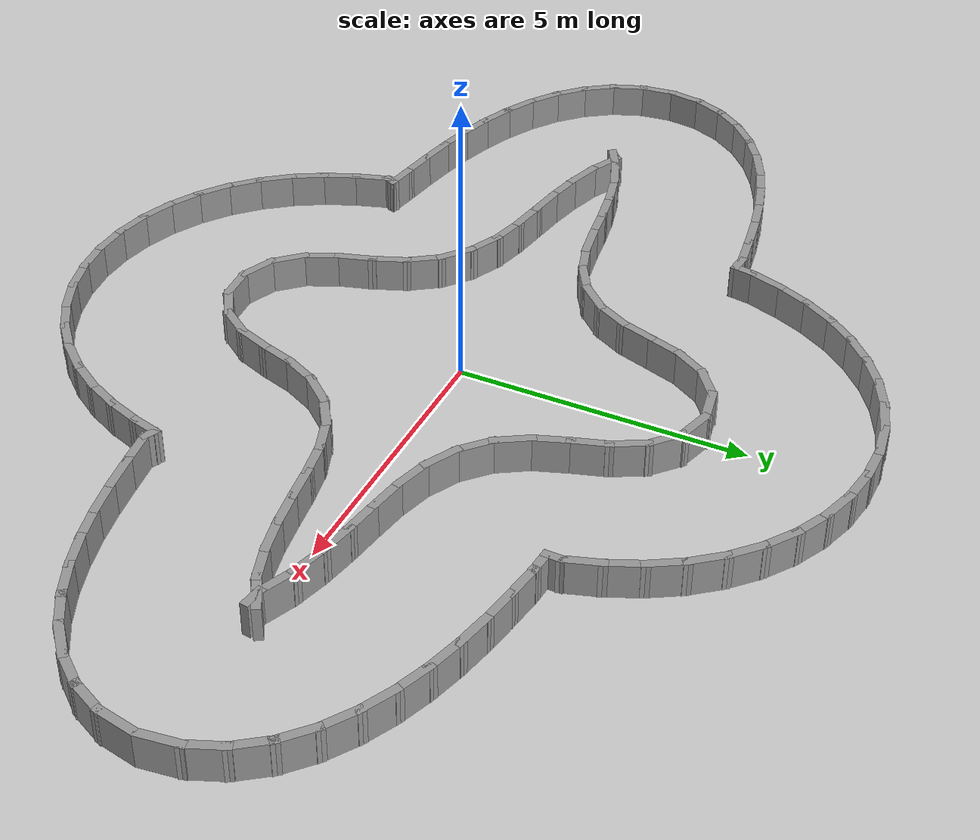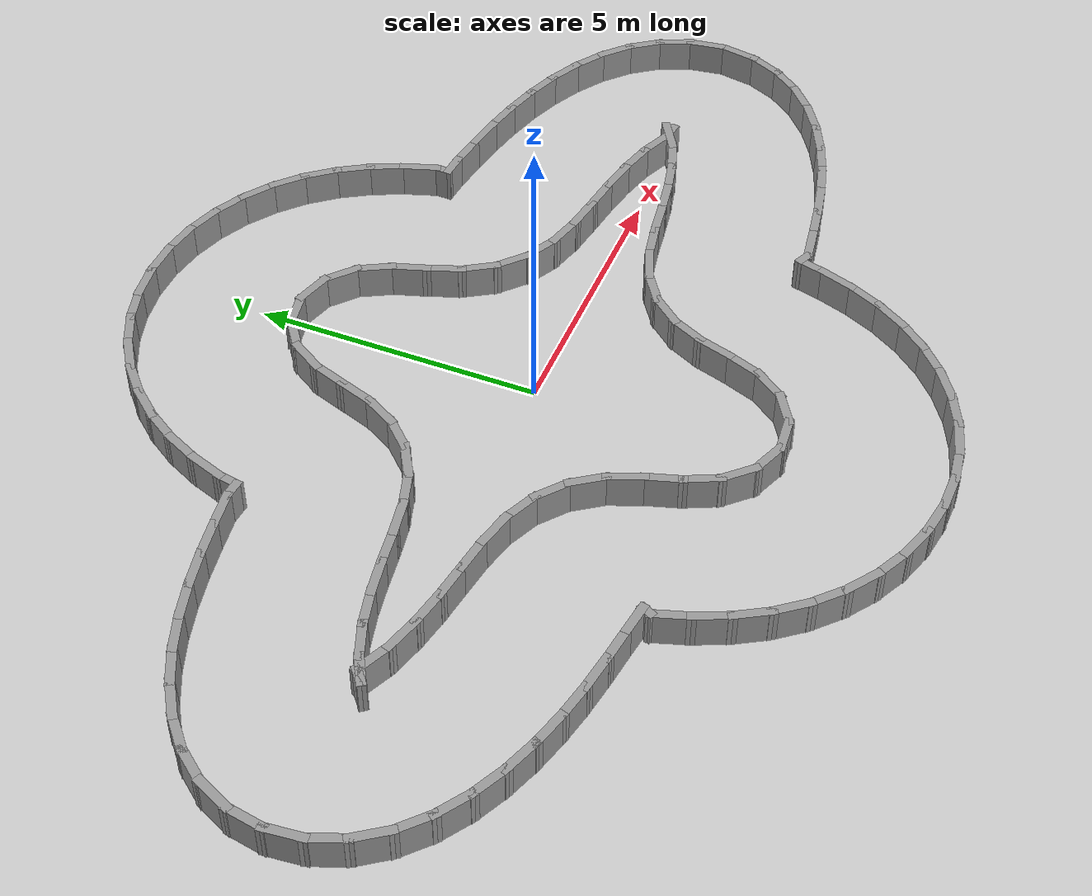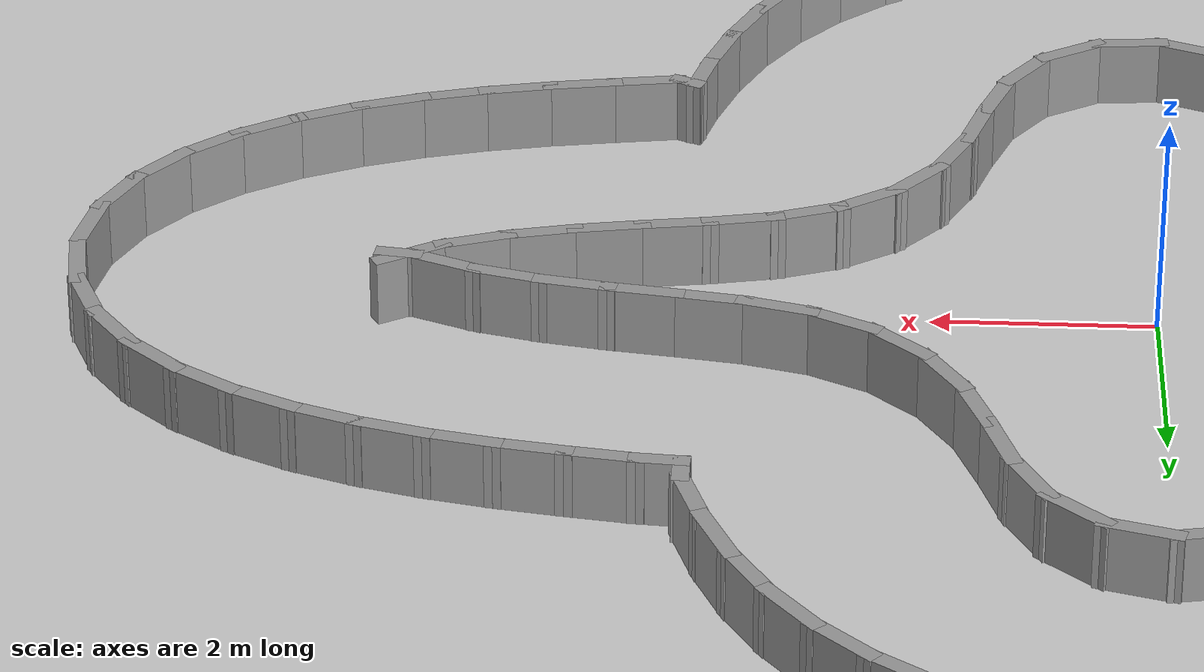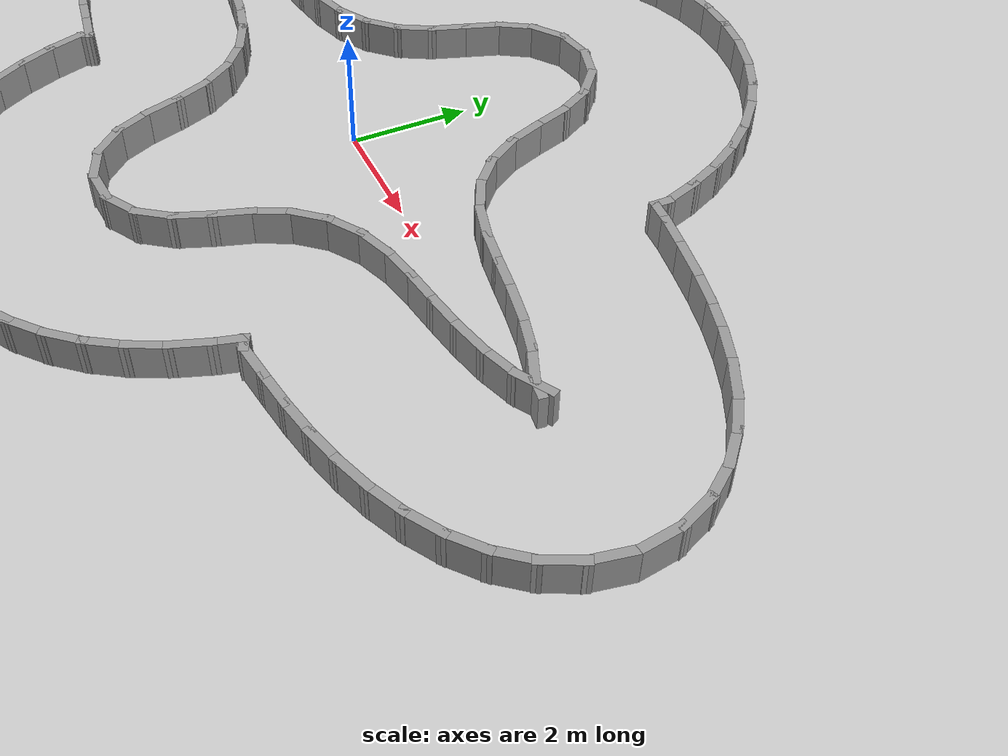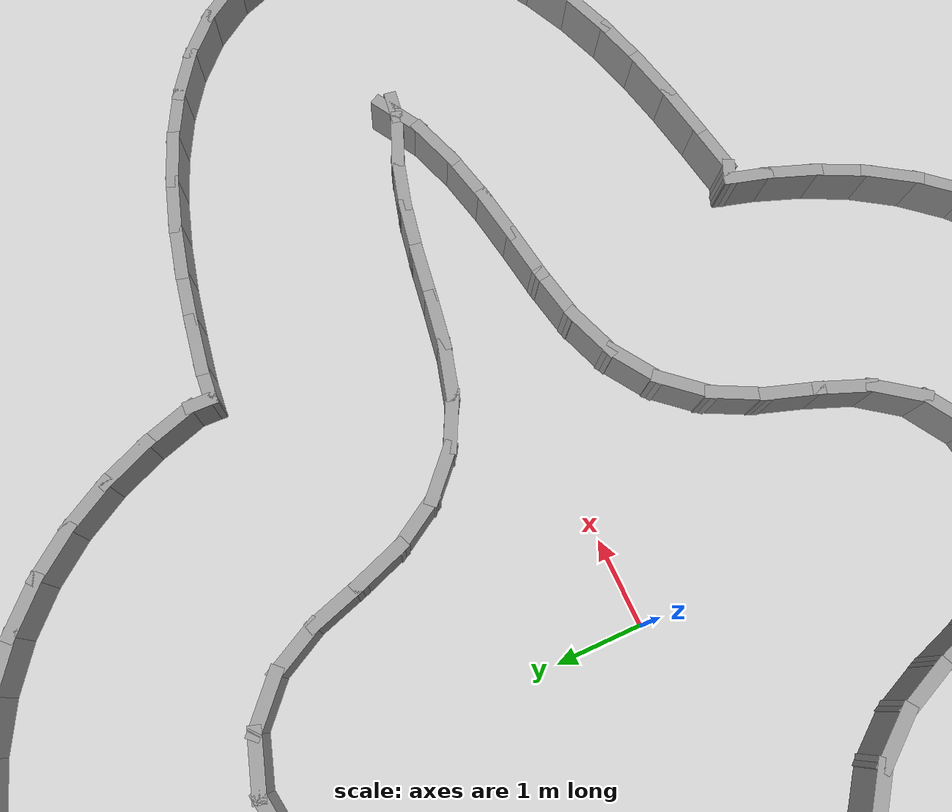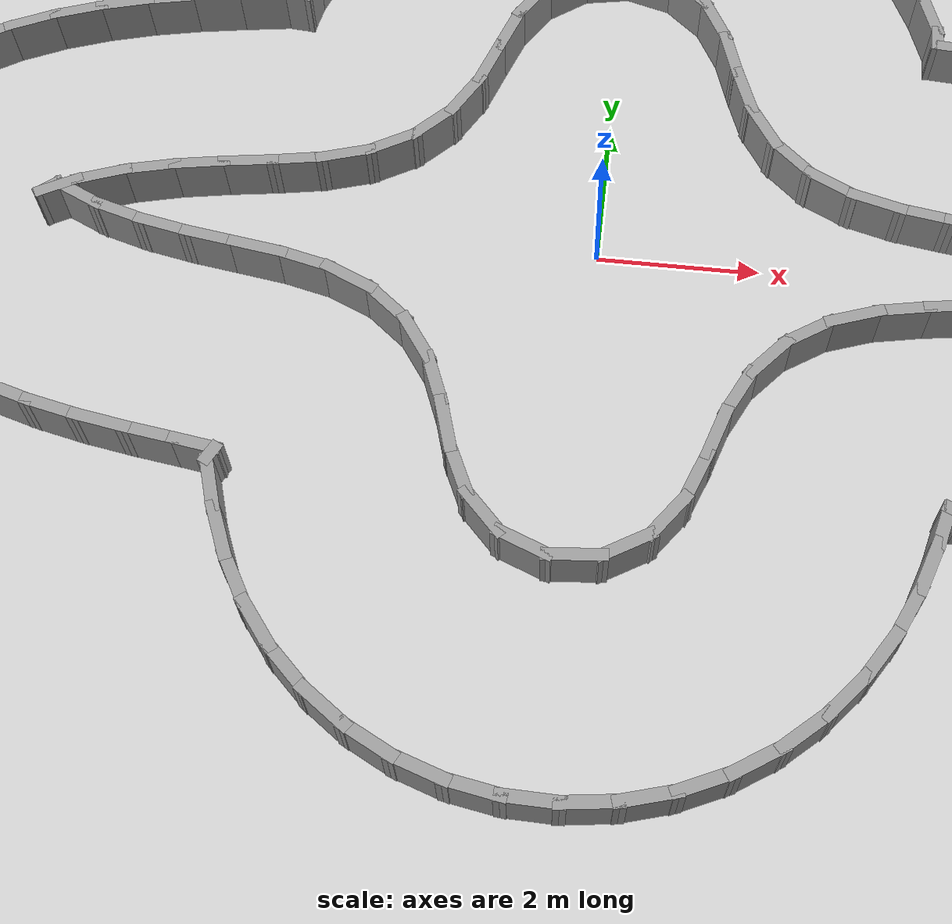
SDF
<?xml version="1.0" ?>
<sdf version='1.7'>
  <world name='default'>
    <plugin name='gazebo_ros_state' filename='libgazebo_ros_state.so'>
      <ros>
        <namespace>/</namespace>
      </ros>
      <update_rate>1000.0</update_rate>
    </plugin>

    <light name='sun' type='directional'>
      <cast_shadows>1</cast_shadows>
      <pose>0 0 10 0 -0 0</pose>
      <diffuse>0.8 0.8 0.8 1</diffuse>
      <specular>0.2 0.2 0.2 1</specular>
      <attenuation>
        <range>1000</range>
        <constant>0.9</constant>
        <linear>0.01</linear>
        <quadratic>0.001</quadratic>
      </attenuation>
      <direction>-0.5 0.1 -0.9</direction>
      <spot>
        <inner_angle>0</inner_angle>
        <outer_angle>0</outer_angle>
        <falloff>0</falloff>
      </spot>
    </light>
    <model name='ground_plane'>
      <static>1</static>
      <link name='link'>
        <collision name='collision'>
          <geometry>
            <plane>
              <normal>0 0 1</normal>
              <size>100 100</size>
            </plane>
          </geometry>
          <surface>
            <friction>
              <ode>
                <mu>100</mu>
                <mu2>50</mu2>
              </ode>
              <torsional>
                <ode/>
              </torsional>
            </friction>
            <contact>
              <ode/>
            </contact>
            <bounce/>
          </surface>
          <max_contacts>10</max_contacts>
        </collision>
        <visual name='visual'>
          <cast_shadows>0</cast_shadows>
          <geometry>
            <plane>
              <normal>0 0 1</normal>
              <size>100 100</size>
            </plane>
          </geometry>
          <material>
            <script>
              <uri>file://media/materials/scripts/gazebo.material</uri>
              <name>Gazebo/Grey</name>
            </script>
          </material>
        </visual>
        <self_collide>0</self_collide>
        <enable_wind>0</enable_wind>
        <kinematic>0</kinematic>
      </link>
    </model>
    <gravity>0 0 -9.8</gravity>
    <magnetic_field>6e-06 2.3e-05 -4.2e-05</magnetic_field>
    <atmosphere type='adiabatic'/>
    <physics type='ode'>
      <max_step_size>0.001</max_step_size>
      <real_time_factor>1</real_time_factor>
      <real_time_update_rate>1000</real_time_update_rate>
    </physics>
    <scene>
      <ambient>0.4 0.4 0.4 1</ambient>
      <background>0.7 0.7 0.7 1</background>
      <shadows>1</shadows>
    </scene>
    <audio>
      <device>default</device>
    </audio>
    <wind/>
    <spherical_coordinates>
      <surface_model>EARTH_WGS84</surface_model>
      <latitude_deg>0</latitude_deg>
      <longitude_deg>0</longitude_deg>
      <elevation>0</elevation>
      <heading_deg>0</heading_deg>
    </spherical_coordinates>
  <model name='rand_lobed_05'>
    <pose>0 0 0 0 -0 0</pose>
    <link name='Wall_0'>
      <collision name='Wall_0_Collision'>
        <geometry><box><size>0.4277 0.1500 0.6000</size></box></geometry>
        <pose>0 0 0.3000 0 -0 0</pose>
      </collision>
      <visual name='Wall_0_Visual'>
        <pose>0 0 0.3000 0 -0 0</pose>
        <geometry><box><size>0.4277 0.1500 0.6000</size></box></geometry>
        <material>
          <script>
            <uri>file://media/materials/scripts/gazebo.material</uri>
            <name>Gazebo/Grey</name>
          </script>
          <ambient>1 1 1 1</ambient>
        </material>
      </visual>
      <pose>6.6623 0.0193 0 0 -0 3.00180</pose>
    </link>
    <link name='Wall_1'>
      <collision name='Wall_1_Collision'>
        <geometry><box><size>0.7492 0.1500 0.6000</size></box></geometry>
        <pose>0 0 0.3000 0 -0 0</pose>
      </collision>
      <visual name='Wall_1_Visual'>
        <pose>0 0 0.3000 0 -0 0</pose>
        <geometry><box><size>0.7492 0.1500 0.6000</size></box></geometry>
        <material>
          <script>
            <uri>file://media/materials/scripts/gazebo.material</uri>
            <name>Gazebo/Grey</name>
          </script>
          <ambient>1 1 1 1</ambient>
        </material>
      </visual>
      <pose>6.2479 0.1531 0 0 -0 2.74974</pose>
    </link>
    <link name='Wall_2'>
      <collision name='Wall_2_Collision'>
        <geometry><box><size>0.7498 0.1500 0.6000</size></box></geometry>
        <pose>0 0 0.3000 0 -0 0</pose>
      </collision>
      <visual name='Wall_2_Visual'>
        <pose>0 0 0.3000 0 -0 0</pose>
        <geometry><box><size>0.7498 0.1500 0.6000</size></box></geometry>
        <material>
          <script>
            <uri>file://media/materials/scripts/gazebo.material</uri>
            <name>Gazebo/Grey</name>
          </script>
          <ambient>1 1 1 1</ambient>
        </material>
      </visual>
      <pose>5.6813 0.3449 0 0 -0 2.88060</pose>
    </link>
    <link name='Wall_3'>
      <collision name='Wall_3_Collision'>
        <geometry><box><size>0.7499 0.1500 0.6000</size></box></geometry>
        <pose>0 0 0.3000 0 -0 0</pose>
      </collision>
      <visual name='Wall_3_Visual'>
        <pose>0 0 0.3000 0 -0 0</pose>
        <geometry><box><size>0.7499 0.1500 0.6000</size></box></geometry>
        <material>
          <script>
            <uri>file://media/materials/scripts/gazebo.material</uri>
            <name>Gazebo/Grey</name>
          </script>
          <ambient>1 1 1 1</ambient>
        </material>
      </visual>
      <pose>5.0966 0.4771 0 0 -0 2.95773</pose>
    </link>
    <link name='Wall_4'>
      <collision name='Wall_4_Collision'>
        <geometry><box><size>0.7500 0.1500 0.6000</size></box></geometry>
        <pose>0 0 0.3000 0 -0 0</pose>
      </collision>
      <visual name='Wall_4_Visual'>
        <pose>0 0 0.3000 0 -0 0</pose>
        <geometry><box><size>0.7500 0.1500 0.6000</size></box></geometry>
        <material>
          <script>
            <uri>file://media/materials/scripts/gazebo.material</uri>
            <name>Gazebo/Grey</name>
          </script>
          <ambient>1 1 1 1</ambient>
        </material>
      </visual>
      <pose>4.5049 0.5756 0 0 -0 2.99577</pose>
    </link>
    <link name='Wall_5'>
      <collision name='Wall_5_Collision'>
        <geometry><box><size>0.7499 0.1500 0.6000</size></box></geometry>
        <pose>0 0 0.3000 0 -0 0</pose>
      </collision>
      <visual name='Wall_5_Visual'>
        <pose>0 0 0.3000 0 -0 0</pose>
        <geometry><box><size>0.7499 0.1500 0.6000</size></box></geometry>
        <material>
          <script>
            <uri>file://media/materials/scripts/gazebo.material</uri>
            <name>Gazebo/Grey</name>
          </script>
          <ambient>1 1 1 1</ambient>
        </material>
      </visual>
      <pose>3.9121 0.6674 0 0 -0 2.98009</pose>
    </link>
    <link name='Wall_6'>
      <collision name='Wall_6_Collision'>
        <geometry><box><size>0.7494 0.1500 0.6000</size></box></geometry>
        <pose>0 0 0.3000 0 -0 0</pose>
      </collision>
      <visual name='Wall_6_Visual'>
        <pose>0 0 0.3000 0 -0 0</pose>
        <geometry><box><size>0.7494 0.1500 0.6000</size></box></geometry>
        <material>
          <script>
            <uri>file://media/materials/scripts/gazebo.material</uri>
            <name>Gazebo/Grey</name>
          </script>
          <ambient>1 1 1 1</ambient>
        </material>
      </visual>
      <pose>3.3268 0.7943 0 0 -0 2.87596</pose>
    </link>
    <link name='Wall_7'>
      <collision name='Wall_7_Collision'>
        <geometry><box><size>0.7484 0.1500 0.6000</size></box></geometry>
        <pose>0 0 0.3000 0 -0 0</pose>
      </collision>
      <visual name='Wall_7_Visual'>
        <pose>0 0 0.3000 0 -0 0</pose>
        <geometry><box><size>0.7484 0.1500 0.6000</size></box></geometry>
        <material>
          <script>
            <uri>file://media/materials/scripts/gazebo.material</uri>
            <name>Gazebo/Grey</name>
          </script>
          <ambient>1 1 1 1</ambient>
        </material>
      </visual>
      <pose>2.7712 1.0092 0 0 -0 2.66891</pose>
    </link>
    <link name='Wall_8'>
      <collision name='Wall_8_Collision'>
        <geometry><box><size>0.7480 0.1500 0.6000</size></box></geometry>
        <pose>0 0 0.3000 0 -0 0</pose>
      </collision>
      <visual name='Wall_8_Visual'>
        <pose>0 0 0.3000 0 -0 0</pose>
        <geometry><box><size>0.7480 0.1500 0.6000</size></box></geometry>
        <material>
          <script>
            <uri>file://media/materials/scripts/gazebo.material</uri>
            <name>Gazebo/Grey</name>
          </script>
          <ambient>1 1 1 1</ambient>
        </material>
      </visual>
      <pose>2.2846 1.3477 0 0 -0 2.39866</pose>
    </link>
    <link name='Wall_9'>
      <collision name='Wall_9_Collision'>
        <geometry><box><size>0.7484 0.1500 0.6000</size></box></geometry>
        <pose>0 0 0.3000 0 -0 0</pose>
      </collision>
      <visual name='Wall_9_Visual'>
        <pose>0 0 0.3000 0 -0 0</pose>
        <geometry><box><size>0.7484 0.1500 0.6000</size></box></geometry>
        <material>
          <script>
            <uri>file://media/materials/scripts/gazebo.material</uri>
            <name>Gazebo/Grey</name>
          </script>
          <ambient>1 1 1 1</ambient>
        </material>
      </visual>
      <pose>1.9070 1.8043 0 0 -0 2.12506</pose>
    </link>
    <link name='Wall_10'>
      <collision name='Wall_10_Collision'>
        <geometry><box><size>0.7495 0.1500 0.6000</size></box></geometry>
        <pose>0 0 0.3000 0 -0 0</pose>
      </collision>
      <visual name='Wall_10_Visual'>
        <pose>0 0 0.3000 0 -0 0</pose>
        <geometry><box><size>0.7495 0.1500 0.6000</size></box></geometry>
        <material>
          <script>
            <uri>file://media/materials/scripts/gazebo.material</uri>
            <name>Gazebo/Grey</name>
          </script>
          <ambient>1 1 1 1</ambient>
        </material>
      </visual>
      <pose>1.6471 2.3404 0 0 -0 1.91933</pose>
    </link>
    <link name='Wall_11'>
      <collision name='Wall_11_Collision'>
        <geometry><box><size>0.7499 0.1500 0.6000</size></box></geometry>
        <pose>0 0 0.3000 0 -0 0</pose>
      </collision>
      <visual name='Wall_11_Visual'>
        <pose>0 0 0.3000 0 -0 0</pose>
        <geometry><box><size>0.7499 0.1500 0.6000</size></box></geometry>
        <material>
          <script>
            <uri>file://media/materials/scripts/gazebo.material</uri>
            <name>Gazebo/Grey</name>
          </script>
          <ambient>1 1 1 1</ambient>
        </material>
      </visual>
      <pose>1.4534 2.9078 0 0 -0 1.88031</pose>
    </link>
    <link name='Wall_12'>
      <collision name='Wall_12_Collision'>
        <geometry><box><size>0.7480 0.1500 0.6000</size></box></geometry>
        <pose>0 0 0.3000 0 -0 0</pose>
      </collision>
      <visual name='Wall_12_Visual'>
        <pose>0 0 0.3000 0 -0 0</pose>
        <geometry><box><size>0.7480 0.1500 0.6000</size></box></geometry>
        <material>
          <script>
            <uri>file://media/materials/scripts/gazebo.material</uri>
            <name>Gazebo/Grey</name>
          </script>
          <ambient>1 1 1 1</ambient>
        </material>
      </visual>
      <pose>1.2215 3.4574 0 0 -0 2.06008</pose>
    </link>
    <link name='Wall_13'>
      <collision name='Wall_13_Collision'>
        <geometry><box><size>0.7456 0.1500 0.6000</size></box></geometry>
        <pose>0 0 0.3000 0 -0 0</pose>
      </collision>
      <visual name='Wall_13_Visual'>
        <pose>0 0 0.3000 0 -0 0</pose>
        <geometry><box><size>0.7456 0.1500 0.6000</size></box></geometry>
        <material>
          <script>
            <uri>file://media/materials/scripts/gazebo.material</uri>
            <name>Gazebo/Grey</name>
          </script>
          <ambient>1 1 1 1</ambient>
        </material>
      </visual>
      <pose>0.8582 3.9190 0 0 -0 2.41609</pose>
    </link>
    <link name='Wall_14'>
      <collision name='Wall_14_Collision'>
        <geometry><box><size>0.7447 0.1500 0.6000</size></box></geometry>
        <pose>0 0 0.3000 0 -0 0</pose>
      </collision>
      <visual name='Wall_14_Visual'>
        <pose>0 0 0.3000 0 -0 0</pose>
        <geometry><box><size>0.7447 0.1500 0.6000</size></box></geometry>
        <material>
          <script>
            <uri>file://media/materials/scripts/gazebo.material</uri>
            <name>Gazebo/Grey</name>
          </script>
          <ambient>1 1 1 1</ambient>
        </material>
      </visual>
      <pose>0.3496 4.1989 0 0 -0 2.86089</pose>
    </link>
    <link name='Wall_15'>
      <collision name='Wall_15_Collision'>
        <geometry><box><size>0.7447 0.1500 0.6000</size></box></geometry>
        <pose>0 0 0.3000 0 -0 0</pose>
      </collision>
      <visual name='Wall_15_Visual'>
        <pose>0 0 0.3000 0 -0 0</pose>
        <geometry><box><size>0.7447 0.1500 0.6000</size></box></geometry>
        <material>
          <script>
            <uri>file://media/materials/scripts/gazebo.material</uri>
            <name>Gazebo/Grey</name>
          </script>
          <ambient>1 1 1 1</ambient>
        </material>
      </visual>
      <pose>-0.2285 4.2274 0 0 -0 -2.95936</pose>
    </link>
    <link name='Wall_16'>
      <collision name='Wall_16_Collision'>
        <geometry><box><size>0.7453 0.1500 0.6000</size></box></geometry>
        <pose>0 0 0.3000 0 -0 0</pose>
      </collision>
      <visual name='Wall_16_Visual'>
        <pose>0 0 0.3000 0 -0 0</pose>
        <geometry><box><size>0.7453 0.1500 0.6000</size></box></geometry>
        <material>
          <script>
            <uri>file://media/materials/scripts/gazebo.material</uri>
            <name>Gazebo/Grey</name>
          </script>
          <ambient>1 1 1 1</ambient>
        </material>
      </visual>
      <pose>-0.7605 3.9970 0 0 -0 -2.50664</pose>
    </link>
    <link name='Wall_17'>
      <collision name='Wall_17_Collision'>
        <geometry><box><size>0.7475 0.1500 0.6000</size></box></geometry>
        <pose>0 0 0.3000 0 -0 0</pose>
      </collision>
      <visual name='Wall_17_Visual'>
        <pose>0 0 0.3000 0 -0 0</pose>
        <geometry><box><size>0.7475 0.1500 0.6000</size></box></geometry>
        <material>
          <script>
            <uri>file://media/materials/scripts/gazebo.material</uri>
            <name>Gazebo/Grey</name>
          </script>
          <ambient>1 1 1 1</ambient>
        </material>
      </visual>
      <pose>-1.1570 3.5662 0 0 -0 -2.12377</pose>
    </link>
    <link name='Wall_18'>
      <collision name='Wall_18_Collision'>
        <geometry><box><size>0.7496 0.1500 0.6000</size></box></geometry>
        <pose>0 0 0.3000 0 -0 0</pose>
      </collision>
      <visual name='Wall_18_Visual'>
        <pose>0 0 0.3000 0 -0 0</pose>
        <geometry><box><size>0.7496 0.1500 0.6000</size></box></geometry>
        <material>
          <script>
            <uri>file://media/materials/scripts/gazebo.material</uri>
            <name>Gazebo/Grey</name>
          </script>
          <ambient>1 1 1 1</ambient>
        </material>
      </visual>
      <pose>-1.4110 3.0284 0 0 -0 -1.90061</pose>
    </link>
    <link name='Wall_19'>
      <collision name='Wall_19_Collision'>
        <geometry><box><size>0.7497 0.1500 0.6000</size></box></geometry>
        <pose>0 0 0.3000 0 -0 0</pose>
      </collision>
      <visual name='Wall_19_Visual'>
        <pose>0 0 0.3000 0 -0 0</pose>
        <geometry><box><size>0.7497 0.1500 0.6000</size></box></geometry>
        <material>
          <script>
            <uri>file://media/materials/scripts/gazebo.material</uri>
            <name>Gazebo/Grey</name>
          </script>
          <ambient>1 1 1 1</ambient>
        </material>
      </visual>
      <pose>-1.6033 2.4604 0 0 -0 -1.89381</pose>
    </link>
    <link name='Wall_20'>
      <collision name='Wall_20_Collision'>
        <geometry><box><size>0.7485 0.1500 0.6000</size></box></geometry>
        <pose>0 0 0.3000 0 -0 0</pose>
      </collision>
      <visual name='Wall_20_Visual'>
        <pose>0 0 0.3000 0 -0 0</pose>
        <geometry><box><size>0.7485 0.1500 0.6000</size></box></geometry>
        <material>
          <script>
            <uri>file://media/materials/scripts/gazebo.material</uri>
            <name>Gazebo/Grey</name>
          </script>
          <ambient>1 1 1 1</ambient>
        </material>
      </visual>
      <pose>-1.8424 1.9136 0 0 -0 -2.07239</pose>
    </link>
    <link name='Wall_21'>
      <collision name='Wall_21_Collision'>
        <geometry><box><size>0.7480 0.1500 0.6000</size></box></geometry>
        <pose>0 0 0.3000 0 -0 0</pose>
      </collision>
      <visual name='Wall_21_Visual'>
        <pose>0 0 0.3000 0 -0 0</pose>
        <geometry><box><size>0.7480 0.1500 0.6000</size></box></geometry>
        <material>
          <script>
            <uri>file://media/materials/scripts/gazebo.material</uri>
            <name>Gazebo/Grey</name>
          </script>
          <ambient>1 1 1 1</ambient>
        </material>
      </visual>
      <pose>-2.1940 1.4361 0 0 -0 -2.33864</pose>
    </link>
    <link name='Wall_22'>
      <collision name='Wall_22_Collision'>
        <geometry><box><size>0.7483 0.1500 0.6000</size></box></geometry>
        <pose>0 0 0.3000 0 -0 0</pose>
      </collision>
      <visual name='Wall_22_Visual'>
        <pose>0 0 0.3000 0 -0 0</pose>
        <geometry><box><size>0.7483 0.1500 0.6000</size></box></geometry>
        <material>
          <script>
            <uri>file://media/materials/scripts/gazebo.material</uri>
            <name>Gazebo/Grey</name>
          </script>
          <ambient>1 1 1 1</ambient>
        </material>
      </visual>
      <pose>-2.6602 1.0706 0 0 -0 -2.61456</pose>
    </link>
    <link name='Wall_23'>
      <collision name='Wall_23_Collision'>
        <geometry><box><size>0.7492 0.1500 0.6000</size></box></geometry>
        <pose>0 0 0.3000 0 -0 0</pose>
      </collision>
      <visual name='Wall_23_Visual'>
        <pose>0 0 0.3000 0 -0 0</pose>
        <geometry><box><size>0.7492 0.1500 0.6000</size></box></geometry>
        <material>
          <script>
            <uri>file://media/materials/scripts/gazebo.material</uri>
            <name>Gazebo/Grey</name>
          </script>
          <ambient>1 1 1 1</ambient>
        </material>
      </visual>
      <pose>-3.2048 0.8311 0 0 -0 -2.83980</pose>
    </link>
    <link name='Wall_24'>
      <collision name='Wall_24_Collision'>
        <geometry><box><size>0.7499 0.1500 0.6000</size></box></geometry>
        <pose>0 0 0.3000 0 -0 0</pose>
      </collision>
      <visual name='Wall_24_Visual'>
        <pose>0 0 0.3000 0 -0 0</pose>
        <geometry><box><size>0.7499 0.1500 0.6000</size></box></geometry>
        <material>
          <script>
            <uri>file://media/materials/scripts/gazebo.material</uri>
            <name>Gazebo/Grey</name>
          </script>
          <ambient>1 1 1 1</ambient>
        </material>
      </visual>
      <pose>-3.7862 0.6898 0 0 -0 -2.96652</pose>
    </link>
    <link name='Wall_25'>
      <collision name='Wall_25_Collision'>
        <geometry><box><size>0.7500 0.1500 0.6000</size></box></geometry>
        <pose>0 0 0.3000 0 -0 0</pose>
      </collision>
      <visual name='Wall_25_Visual'>
        <pose>0 0 0.3000 0 -0 0</pose>
        <geometry><box><size>0.7500 0.1500 0.6000</size></box></geometry>
        <material>
          <script>
            <uri>file://media/materials/scripts/gazebo.material</uri>
            <name>Gazebo/Grey</name>
          </script>
          <ambient>1 1 1 1</ambient>
        </material>
      </visual>
      <pose>-4.3784 0.5946 0 0 -0 -2.99791</pose>
    </link>
    <link name='Wall_26'>
      <collision name='Wall_26_Collision'>
        <geometry><box><size>0.7499 0.1500 0.6000</size></box></geometry>
        <pose>0 0 0.3000 0 -0 0</pose>
      </collision>
      <visual name='Wall_26_Visual'>
        <pose>0 0 0.3000 0 -0 0</pose>
        <geometry><box><size>0.7499 0.1500 0.6000</size></box></geometry>
        <material>
          <script>
            <uri>file://media/materials/scripts/gazebo.material</uri>
            <name>Gazebo/Grey</name>
          </script>
          <ambient>1 1 1 1</ambient>
        </material>
      </visual>
      <pose>-4.9709 0.5002 0 0 -0 -2.96922</pose>
    </link>
    <link name='Wall_27'>
      <collision name='Wall_27_Collision'>
        <geometry><box><size>0.7498 0.1500 0.6000</size></box></geometry>
        <pose>0 0 0.3000 0 -0 0</pose>
      </collision>
      <visual name='Wall_27_Visual'>
        <pose>0 0 0.3000 0 -0 0</pose>
        <geometry><box><size>0.7498 0.1500 0.6000</size></box></geometry>
        <material>
          <script>
            <uri>file://media/materials/scripts/gazebo.material</uri>
            <name>Gazebo/Grey</name>
          </script>
          <ambient>1 1 1 1</ambient>
        </material>
      </visual>
      <pose>-5.5576 0.3771 0 0 -0 -2.90050</pose>
    </link>
    <link name='Wall_28'>
      <collision name='Wall_28_Collision'>
        <geometry><box><size>0.7494 0.1500 0.6000</size></box></geometry>
        <pose>0 0 0.3000 0 -0 0</pose>
      </collision>
      <visual name='Wall_28_Visual'>
        <pose>0 0 0.3000 0 -0 0</pose>
        <geometry><box><size>0.7494 0.1500 0.6000</size></box></geometry>
        <material>
          <script>
            <uri>file://media/materials/scripts/gazebo.material</uri>
            <name>Gazebo/Grey</name>
          </script>
          <ambient>1 1 1 1</ambient>
        </material>
      </visual>
      <pose>-6.1297 0.2008 0 0 -0 -2.78472</pose>
    </link>
    <link name='Wall_29'>
      <collision name='Wall_29_Collision'>
        <geometry><box><size>0.6137 0.1500 0.6000</size></box></geometry>
        <pose>0 0 0.3000 0 -0 0</pose>
      </collision>
      <visual name='Wall_29_Visual'>
        <pose>0 0 0.3000 0 -0 0</pose>
        <geometry><box><size>0.6137 0.1500 0.6000</size></box></geometry>
        <material>
          <script>
            <uri>file://media/materials/scripts/gazebo.material</uri>
            <name>Gazebo/Grey</name>
          </script>
          <ambient>1 1 1 1</ambient>
        </material>
      </visual>
      <pose>-6.6139 -0.0151 0 0 -0 -2.64142</pose>
    </link>
    <link name='Wall_30'>
      <collision name='Wall_30_Collision'>
        <geometry><box><size>0.3865 0.1500 0.6000</size></box></geometry>
        <pose>0 0 0.3000 0 -0 0</pose>
      </collision>
      <visual name='Wall_30_Visual'>
        <pose>0 0 0.3000 0 -0 0</pose>
        <geometry><box><size>0.3865 0.1500 0.6000</size></box></geometry>
        <material>
          <script>
            <uri>file://media/materials/scripts/gazebo.material</uri>
            <name>Gazebo/Grey</name>
          </script>
          <ambient>1 1 1 1</ambient>
        </material>
      </visual>
      <pose>-6.7265 -0.0506 0 0 -0 0.69460</pose>
    </link>
    <link name='Wall_31'>
      <collision name='Wall_31_Collision'>
        <geometry><box><size>0.7489 0.1500 0.6000</size></box></geometry>
        <pose>0 0 0.3000 0 -0 0</pose>
      </collision>
      <visual name='Wall_31_Visual'>
        <pose>0 0 0.3000 0 -0 0</pose>
        <geometry><box><size>0.7489 0.1500 0.6000</size></box></geometry>
        <material>
          <script>
            <uri>file://media/materials/scripts/gazebo.material</uri>
            <name>Gazebo/Grey</name>
          </script>
          <ambient>1 1 1 1</ambient>
        </material>
      </visual>
      <pose>-6.3639 -0.1006 0 0 -0 -0.43334</pose>
    </link>
    <link name='Wall_32'>
      <collision name='Wall_32_Collision'>
        <geometry><box><size>0.7497 0.1500 0.6000</size></box></geometry>
        <pose>0 0 0.3000 0 -0 0</pose>
      </collision>
      <visual name='Wall_32_Visual'>
        <pose>0 0 0.3000 0 -0 0</pose>
        <geometry><box><size>0.7497 0.1500 0.6000</size></box></geometry>
        <material>
          <script>
            <uri>file://media/materials/scripts/gazebo.material</uri>
            <name>Gazebo/Grey</name>
          </script>
          <ambient>1 1 1 1</ambient>
        </material>
      </visual>
      <pose>-5.8042 -0.3101 0 0 -0 -0.28306</pose>
    </link>
    <link name='Wall_33'>
      <collision name='Wall_33_Collision'>
        <geometry><box><size>0.7499 0.1500 0.6000</size></box></geometry>
        <pose>0 0 0.3000 0 -0 0</pose>
      </collision>
      <visual name='Wall_33_Visual'>
        <pose>0 0 0.3000 0 -0 0</pose>
        <geometry><box><size>0.7499 0.1500 0.6000</size></box></geometry>
        <material>
          <script>
            <uri>file://media/materials/scripts/gazebo.material</uri>
            <name>Gazebo/Grey</name>
          </script>
          <ambient>1 1 1 1</ambient>
        </material>
      </visual>
      <pose>-5.2221 -0.4526 0 0 -0 -0.19705</pose>
    </link>
    <link name='Wall_34'>
      <collision name='Wall_34_Collision'>
        <geometry><box><size>0.7500 0.1500 0.6000</size></box></geometry>
        <pose>0 0 0.3000 0 -0 0</pose>
      </collision>
      <visual name='Wall_34_Visual'>
        <pose>0 0 0.3000 0 -0 0</pose>
        <geometry><box><size>0.7500 0.1500 0.6000</size></box></geometry>
        <material>
          <script>
            <uri>file://media/materials/scripts/gazebo.material</uri>
            <name>Gazebo/Grey</name>
          </script>
          <ambient>1 1 1 1</ambient>
        </material>
      </visual>
      <pose>-4.6314 -0.5562 0 0 -0 -0.15031</pose>
    </link>
    <link name='Wall_35'>
      <collision name='Wall_35_Collision'>
        <geometry><box><size>0.7500 0.1500 0.6000</size></box></geometry>
        <pose>0 0 0.3000 0 -0 0</pose>
      </collision>
      <visual name='Wall_35_Visual'>
        <pose>0 0 0.3000 0 -0 0</pose>
        <geometry><box><size>0.7500 0.1500 0.6000</size></box></geometry>
        <material>
          <script>
            <uri>file://media/materials/scripts/gazebo.material</uri>
            <name>Gazebo/Grey</name>
          </script>
          <ambient>1 1 1 1</ambient>
        </material>
      </visual>
      <pose>-4.0382 -0.6466 0 0 -0 -0.15204</pose>
    </link>
    <link name='Wall_36'>
      <collision name='Wall_36_Collision'>
        <geometry><box><size>0.7495 0.1500 0.6000</size></box></geometry>
        <pose>0 0 0.3000 0 -0 0</pose>
      </collision>
      <visual name='Wall_36_Visual'>
        <pose>0 0 0.3000 0 -0 0</pose>
        <geometry><box><size>0.7495 0.1500 0.6000</size></box></geometry>
        <material>
          <script>
            <uri>file://media/materials/scripts/gazebo.material</uri>
            <name>Gazebo/Grey</name>
          </script>
          <ambient>1 1 1 1</ambient>
        </material>
      </visual>
      <pose>-3.4501 -0.7616 0 0 -0 -0.23445</pose>
    </link>
    <link name='Wall_37'>
      <collision name='Wall_37_Collision'>
        <geometry><box><size>0.7486 0.1500 0.6000</size></box></geometry>
        <pose>0 0 0.3000 0 -0 0</pose>
      </collision>
      <visual name='Wall_37_Visual'>
        <pose>0 0 0.3000 0 -0 0</pose>
        <geometry><box><size>0.7486 0.1500 0.6000</size></box></geometry>
        <material>
          <script>
            <uri>file://media/materials/scripts/gazebo.material</uri>
            <name>Gazebo/Grey</name>
          </script>
          <ambient>1 1 1 1</ambient>
        </material>
      </visual>
      <pose>-2.8854 -0.9537 0 0 -0 -0.42127</pose>
    </link>
    <link name='Wall_38'>
      <collision name='Wall_38_Collision'>
        <geometry><box><size>0.7480 0.1500 0.6000</size></box></geometry>
        <pose>0 0 0.3000 0 -0 0</pose>
      </collision>
      <visual name='Wall_38_Visual'>
        <pose>0 0 0.3000 0 -0 0</pose>
        <geometry><box><size>0.7480 0.1500 0.6000</size></box></geometry>
        <material>
          <script>
            <uri>file://media/materials/scripts/gazebo.material</uri>
            <name>Gazebo/Grey</name>
          </script>
          <ambient>1 1 1 1</ambient>
        </material>
      </visual>
      <pose>-2.3803 -1.2648 0 0 -0 -0.68290</pose>
    </link>
    <link name='Wall_39'>
      <collision name='Wall_39_Collision'>
        <geometry><box><size>0.7482 0.1500 0.6000</size></box></geometry>
        <pose>0 0 0.3000 0 -0 0</pose>
      </collision>
      <visual name='Wall_39_Visual'>
        <pose>0 0 0.3000 0 -0 0</pose>
        <geometry><box><size>0.7482 0.1500 0.6000</size></box></geometry>
        <material>
          <script>
            <uri>file://media/materials/scripts/gazebo.material</uri>
            <name>Gazebo/Grey</name>
          </script>
          <ambient>1 1 1 1</ambient>
        </material>
      </visual>
      <pose>-1.9771 -1.6987 0 0 -0 -0.96118</pose>
    </link>
    <link name='Wall_40'>
      <collision name='Wall_40_Collision'>
        <geometry><box><size>0.7492 0.1500 0.6000</size></box></geometry>
        <pose>0 0 0.3000 0 -0 0</pose>
      </collision>
      <visual name='Wall_40_Visual'>
        <pose>0 0 0.3000 0 -0 0</pose>
        <geometry><box><size>0.7492 0.1500 0.6000</size></box></geometry>
        <material>
          <script>
            <uri>file://media/materials/scripts/gazebo.material</uri>
            <name>Gazebo/Grey</name>
          </script>
          <ambient>1 1 1 1</ambient>
        </material>
      </visual>
      <pose>-1.6942 -2.2219 0 0 -0 -1.18884</pose>
    </link>
    <link name='Wall_41'>
      <collision name='Wall_41_Collision'>
        <geometry><box><size>0.7500 0.1500 0.6000</size></box></geometry>
        <pose>0 0 0.3000 0 -0 0</pose>
      </collision>
      <visual name='Wall_41_Visual'>
        <pose>0 0 0.3000 0 -0 0</pose>
        <geometry><box><size>0.7500 0.1500 0.6000</size></box></geometry>
        <material>
          <script>
            <uri>file://media/materials/scripts/gazebo.material</uri>
            <name>Gazebo/Grey</name>
          </script>
          <ambient>1 1 1 1</ambient>
        </material>
      </visual>
      <pose>-1.4940 -2.7866 0 0 -0 -1.27118</pose>
    </link>
    <link name='Wall_42'>
      <collision name='Wall_42_Collision'>
        <geometry><box><size>0.7485 0.1500 0.6000</size></box></geometry>
        <pose>0 0 0.3000 0 -0 0</pose>
      </collision>
      <visual name='Wall_42_Visual'>
        <pose>0 0 0.3000 0 -0 0</pose>
        <geometry><box><size>0.7485 0.1500 0.6000</size></box></geometry>
        <material>
          <script>
            <uri>file://media/materials/scripts/gazebo.material</uri>
            <name>Gazebo/Grey</name>
          </script>
          <ambient>1 1 1 1</ambient>
        </material>
      </visual>
      <pose>-1.2797 -3.3447 0 0 -0 -1.13705</pose>
    </link>
    <link name='Wall_43'>
      <collision name='Wall_43_Collision'>
        <geometry><box><size>0.7461 0.1500 0.6000</size></box></geometry>
        <pose>0 0 0.3000 0 -0 0</pose>
      </collision>
      <visual name='Wall_43_Visual'>
        <pose>0 0 0.3000 0 -0 0</pose>
        <geometry><box><size>0.7461 0.1500 0.6000</size></box></geometry>
        <material>
          <script>
            <uri>file://media/materials/scripts/gazebo.material</uri>
            <name>Gazebo/Grey</name>
          </script>
          <ambient>1 1 1 1</ambient>
        </material>
      </visual>
      <pose>-0.9489 -3.8326 0 0 -0 -0.81211</pose>
    </link>
    <link name='Wall_44'>
      <collision name='Wall_44_Collision'>
        <geometry><box><size>0.7448 0.1500 0.6000</size></box></geometry>
        <pose>0 0 0.3000 0 -0 0</pose>
      </collision>
      <visual name='Wall_44_Visual'>
        <pose>0 0 0.3000 0 -0 0</pose>
        <geometry><box><size>0.7448 0.1500 0.6000</size></box></geometry>
        <material>
          <script>
            <uri>file://media/materials/scripts/gazebo.material</uri>
            <name>Gazebo/Grey</name>
          </script>
          <ambient>1 1 1 1</ambient>
        </material>
      </visual>
      <pose>-0.4675 -4.1588 0 0 -0 -0.37857</pose>
    </link>
    <link name='Wall_45'>
      <collision name='Wall_45_Collision'>
        <geometry><box><size>0.7446 0.1500 0.6000</size></box></geometry>
        <pose>0 0 0.3000 0 -0 0</pose>
      </collision>
      <visual name='Wall_45_Visual'>
        <pose>0 0 0.3000 0 -0 0</pose>
        <geometry><box><size>0.7446 0.1500 0.6000</size></box></geometry>
        <material>
          <script>
            <uri>file://media/materials/scripts/gazebo.material</uri>
            <name>Gazebo/Grey</name>
          </script>
          <ambient>1 1 1 1</ambient>
        </material>
      </visual>
      <pose>0.1051 -4.2439 0 0 -0 0.08353</pose>
    </link>
    <link name='Wall_46'>
      <collision name='Wall_46_Collision'>
        <geometry><box><size>0.7450 0.1500 0.6000</size></box></geometry>
        <pose>0 0 0.3000 0 -0 0</pose>
      </collision>
      <visual name='Wall_46_Visual'>
        <pose>0 0 0.3000 0 -0 0</pose>
        <geometry><box><size>0.7450 0.1500 0.6000</size></box></geometry>
        <material>
          <script>
            <uri>file://media/materials/scripts/gazebo.material</uri>
            <name>Gazebo/Grey</name>
          </script>
          <ambient>1 1 1 1</ambient>
        </material>
      </visual>
      <pose>0.6564 -4.0658 0 0 -0 0.54134</pose>
    </link>
    <link name='Wall_47'>
      <collision name='Wall_47_Collision'>
        <geometry><box><size>0.7469 0.1500 0.6000</size></box></geometry>
        <pose>0 0 0.3000 0 -0 0</pose>
      </collision>
      <visual name='Wall_47_Visual'>
        <pose>0 0 0.3000 0 -0 0</pose>
        <geometry><box><size>0.7469 0.1500 0.6000</size></box></geometry>
        <material>
          <script>
            <uri>file://media/materials/scripts/gazebo.material</uri>
            <name>Gazebo/Grey</name>
          </script>
          <ambient>1 1 1 1</ambient>
        </material>
      </visual>
      <pose>1.0857 -3.6703 0 0 -0 0.94672</pose>
    </link>
    <link name='Wall_48'>
      <collision name='Wall_48_Collision'>
        <geometry><box><size>0.7493 0.1500 0.6000</size></box></geometry>
        <pose>0 0 0.3000 0 -0 0</pose>
      </collision>
      <visual name='Wall_48_Visual'>
        <pose>0 0 0.3000 0 -0 0</pose>
        <geometry><box><size>0.7493 0.1500 0.6000</size></box></geometry>
        <material>
          <script>
            <uri>file://media/materials/scripts/gazebo.material</uri>
            <name>Gazebo/Grey</name>
          </script>
          <ambient>1 1 1 1</ambient>
        </material>
      </visual>
      <pose>1.3658 -3.1477 0 0 -0 1.21052</pose>
    </link>
    <link name='Wall_49'>
      <collision name='Wall_49_Collision'>
        <geometry><box><size>0.7499 0.1500 0.6000</size></box></geometry>
        <pose>0 0 0.3000 0 -0 0</pose>
      </collision>
      <visual name='Wall_49_Visual'>
        <pose>0 0 0.3000 0 -0 0</pose>
        <geometry><box><size>0.7499 0.1500 0.6000</size></box></geometry>
        <material>
          <script>
            <uri>file://media/materials/scripts/gazebo.material</uri>
            <name>Gazebo/Grey</name>
          </script>
          <ambient>1 1 1 1</ambient>
        </material>
      </visual>
      <pose>1.5618 -2.5813 0 0 -0 1.26466</pose>
    </link>
    <link name='Wall_50'>
      <collision name='Wall_50_Collision'>
        <geometry><box><size>0.7488 0.1500 0.6000</size></box></geometry>
        <pose>0 0 0.3000 0 -0 0</pose>
      </collision>
      <visual name='Wall_50_Visual'>
        <pose>0 0 0.3000 0 -0 0</pose>
        <geometry><box><size>0.7488 0.1500 0.6000</size></box></geometry>
        <material>
          <script>
            <uri>file://media/materials/scripts/gazebo.material</uri>
            <name>Gazebo/Grey</name>
          </script>
          <ambient>1 1 1 1</ambient>
        </material>
      </visual>
      <pose>1.7832 -2.0260 0 0 -0 1.11797</pose>
    </link>
    <link name='Wall_51'>
      <collision name='Wall_51_Collision'>
        <geometry><box><size>0.7480 0.1500 0.6000</size></box></geometry>
        <pose>0 0 0.3000 0 -0 0</pose>
      </collision>
      <visual name='Wall_51_Visual'>
        <pose>0 0 0.3000 0 -0 0</pose>
        <geometry><box><size>0.7480 0.1500 0.6000</size></box></geometry>
        <material>
          <script>
            <uri>file://media/materials/scripts/gazebo.material</uri>
            <name>Gazebo/Grey</name>
          </script>
          <ambient>1 1 1 1</ambient>
        </material>
      </visual>
      <pose>2.1087 -1.5297 0 0 -0 0.86271</pose>
    </link>
    <link name='Wall_52'>
      <collision name='Wall_52_Collision'>
        <geometry><box><size>0.7482 0.1500 0.6000</size></box></geometry>
        <pose>0 0 0.3000 0 -0 0</pose>
      </collision>
      <visual name='Wall_52_Visual'>
        <pose>0 0 0.3000 0 -0 0</pose>
        <geometry><box><size>0.7482 0.1500 0.6000</size></box></geometry>
        <material>
          <script>
            <uri>file://media/materials/scripts/gazebo.material</uri>
            <name>Gazebo/Grey</name>
          </script>
          <ambient>1 1 1 1</ambient>
        </material>
      </visual>
      <pose>2.5527 -1.1378 0 0 -0 0.58359</pose>
    </link>
    <link name='Wall_53'>
      <collision name='Wall_53_Collision'>
        <geometry><box><size>0.7490 0.1500 0.6000</size></box></geometry>
        <pose>0 0 0.3000 0 -0 0</pose>
      </collision>
      <visual name='Wall_53_Visual'>
        <pose>0 0 0.3000 0 -0 0</pose>
        <geometry><box><size>0.7490 0.1500 0.6000</size></box></geometry>
        <material>
          <script>
            <uri>file://media/materials/scripts/gazebo.material</uri>
            <name>Gazebo/Grey</name>
          </script>
          <ambient>1 1 1 1</ambient>
        </material>
      </visual>
      <pose>3.0843 -0.8723 0 0 -0 0.34270</pose>
    </link>
    <link name='Wall_54'>
      <collision name='Wall_54_Collision'>
        <geometry><box><size>0.7498 0.1500 0.6000</size></box></geometry>
        <pose>0 0 0.3000 0 -0 0</pose>
      </collision>
      <visual name='Wall_54_Visual'>
        <pose>0 0 0.3000 0 -0 0</pose>
        <geometry><box><size>0.7498 0.1500 0.6000</size></box></geometry>
        <material>
          <script>
            <uri>file://media/materials/scripts/gazebo.material</uri>
            <name>Gazebo/Grey</name>
          </script>
          <ambient>1 1 1 1</ambient>
        </material>
      </visual>
      <pose>3.6607 -0.7142 0 0 -0 0.19302</pose>
    </link>
    <link name='Wall_55'>
      <collision name='Wall_55_Collision'>
        <geometry><box><size>0.7500 0.1500 0.6000</size></box></geometry>
        <pose>0 0 0.3000 0 -0 0</pose>
      </collision>
      <visual name='Wall_55_Visual'>
        <pose>0 0 0.3000 0 -0 0</pose>
        <geometry><box><size>0.7500 0.1500 0.6000</size></box></geometry>
        <material>
          <script>
            <uri>file://media/materials/scripts/gazebo.material</uri>
            <name>Gazebo/Grey</name>
          </script>
          <ambient>1 1 1 1</ambient>
        </material>
      </visual>
      <pose>4.2519 -0.6135 0 0 -0 0.14419</pose>
    </link>
    <link name='Wall_56'>
      <collision name='Wall_56_Collision'>
        <geometry><box><size>0.7500 0.1500 0.6000</size></box></geometry>
        <pose>0 0 0.3000 0 -0 0</pose>
      </collision>
      <visual name='Wall_56_Visual'>
        <pose>0 0 0.3000 0 -0 0</pose>
        <geometry><box><size>0.7500 0.1500 0.6000</size></box></geometry>
        <material>
          <script>
            <uri>file://media/materials/scripts/gazebo.material</uri>
            <name>Gazebo/Grey</name>
          </script>
          <ambient>1 1 1 1</ambient>
        </material>
      </visual>
      <pose>4.8448 -0.5219 0 0 -0 0.16259</pose>
    </link>
    <link name='Wall_57'>
      <collision name='Wall_57_Collision'>
        <geometry><box><size>0.7498 0.1500 0.6000</size></box></geometry>
        <pose>0 0 0.3000 0 -0 0</pose>
      </collision>
      <visual name='Wall_57_Visual'>
        <pose>0 0 0.3000 0 -0 0</pose>
        <geometry><box><size>0.7498 0.1500 0.6000</size></box></geometry>
        <material>
          <script>
            <uri>file://media/materials/scripts/gazebo.material</uri>
            <name>Gazebo/Grey</name>
          </script>
          <ambient>1 1 1 1</ambient>
        </material>
      </visual>
      <pose>5.4333 -0.4069 0 0 -0 0.22321</pose>
    </link>
    <link name='Wall_58'>
      <collision name='Wall_58_Collision'>
        <geometry><box><size>0.7496 0.1500 0.6000</size></box></geometry>
        <pose>0 0 0.3000 0 -0 0</pose>
      </collision>
      <visual name='Wall_58_Visual'>
        <pose>0 0 0.3000 0 -0 0</pose>
        <geometry><box><size>0.7496 0.1500 0.6000</size></box></geometry>
        <material>
          <script>
            <uri>file://media/materials/scripts/gazebo.material</uri>
            <name>Gazebo/Grey</name>
          </script>
          <ambient>1 1 1 1</ambient>
        </material>
      </visual>
      <pose>6.0098 -0.2444 0 0 -0 0.32653</pose>
    </link>
    <link name='Wall_59'>
      <collision name='Wall_59_Collision'>
        <geometry><box><size>0.7473 0.1500 0.6000</size></box></geometry>
        <pose>0 0 0.3000 0 -0 0</pose>
      </collision>
      <visual name='Wall_59_Visual'>
        <pose>0 0 0.3000 0 -0 0</pose>
        <geometry><box><size>0.7473 0.1500 0.6000</size></box></geometry>
        <material>
          <script>
            <uri>file://media/materials/scripts/gazebo.material</uri>
            <name>Gazebo/Grey</name>
          </script>
          <ambient>1 1 1 1</ambient>
        </material>
      </visual>
      <pose>6.5513 0.0028 0 0 -0 0.53036</pose>
    </link>
    <link name='Wall_60'>
      <collision name='Wall_60_Collision'>
        <geometry><box><size>0.7482 0.1500 0.6000</size></box></geometry>
        <pose>0 0 0.3000 0 -0 0</pose>
      </collision>
      <visual name='Wall_60_Visual'>
        <pose>0 0 0.3000 0 -0 0</pose>
        <geometry><box><size>0.7482 0.1500 0.6000</size></box></geometry>
        <material>
          <script>
            <uri>file://media/materials/scripts/gazebo.material</uri>
            <name>Gazebo/Grey</name>
          </script>
          <ambient>1 1 1 1</ambient>
        </material>
      </visual>
      <pose>9.4550 0.2964 0 0 -0 1.70557</pose>
    </link>
    <link name='Wall_61'>
      <collision name='Wall_61_Collision'>
        <geometry><box><size>0.7484 0.1500 0.6000</size></box></geometry>
        <pose>0 0 0.3000 0 -0 0</pose>
      </collision>
      <visual name='Wall_61_Visual'>
        <pose>0 0 0.3000 0 -0 0</pose>
        <geometry><box><size>0.7484 0.1500 0.6000</size></box></geometry>
        <material>
          <script>
            <uri>file://media/materials/scripts/gazebo.material</uri>
            <name>Gazebo/Grey</name>
          </script>
          <ambient>1 1 1 1</ambient>
        </material>
      </visual>
      <pose>9.2999 0.8690 0 0 -0 1.96512</pose>
    </link>
    <link name='Wall_62'>
      <collision name='Wall_62_Collision'>
        <geometry><box><size>0.7488 0.1500 0.6000</size></box></geometry>
        <pose>0 0 0.3000 0 -0 0</pose>
      </collision>
      <visual name='Wall_62_Visual'>
        <pose>0 0 0.3000 0 -0 0</pose>
        <geometry><box><size>0.7488 0.1500 0.6000</size></box></geometry>
        <material>
          <script>
            <uri>file://media/materials/scripts/gazebo.material</uri>
            <name>Gazebo/Grey</name>
          </script>
          <ambient>1 1 1 1</ambient>
        </material>
      </visual>
      <pose>9.0086 1.3873 0 0 -0 2.20027</pose>
    </link>
    <link name='Wall_63'>
      <collision name='Wall_63_Collision'>
        <geometry><box><size>0.7492 0.1500 0.6000</size></box></geometry>
        <pose>0 0 0.3000 0 -0 0</pose>
      </collision>
      <visual name='Wall_63_Visual'>
        <pose>0 0 0.3000 0 -0 0</pose>
        <geometry><box><size>0.7492 0.1500 0.6000</size></box></geometry>
        <material>
          <script>
            <uri>file://media/materials/scripts/gazebo.material</uri>
            <name>Gazebo/Grey</name>
          </script>
          <ambient>1 1 1 1</ambient>
        </material>
      </visual>
      <pose>8.6116 1.8318 0 0 -0 2.39923</pose>
    </link>
    <link name='Wall_64'>
      <collision name='Wall_64_Collision'>
        <geometry><box><size>0.7495 0.1500 0.6000</size></box></geometry>
        <pose>0 0 0.3000 0 -0 0</pose>
      </collision>
      <visual name='Wall_64_Visual'>
        <pose>0 0 0.3000 0 -0 0</pose>
        <geometry><box><size>0.7495 0.1500 0.6000</size></box></geometry>
        <material>
          <script>
            <uri>file://media/materials/scripts/gazebo.material</uri>
            <name>Gazebo/Grey</name>
          </script>
          <ambient>1 1 1 1</ambient>
        </material>
      </visual>
      <pose>8.1404 2.1991 0 0 -0 2.55971</pose>
    </link>
    <link name='Wall_65'>
      <collision name='Wall_65_Collision'>
        <geometry><box><size>0.7497 0.1500 0.6000</size></box></geometry>
        <pose>0 0 0.3000 0 -0 0</pose>
      </collision>
      <visual name='Wall_65_Visual'>
        <pose>0 0 0.3000 0 -0 0</pose>
        <geometry><box><size>0.7497 0.1500 0.6000</size></box></geometry>
        <material>
          <script>
            <uri>file://media/materials/scripts/gazebo.material</uri>
            <name>Gazebo/Grey</name>
          </script>
          <ambient>1 1 1 1</ambient>
        </material>
      </visual>
      <pose>7.6207 2.4956 0 0 -0 2.68655</pose>
    </link>
    <link name='Wall_66'>
      <collision name='Wall_66_Collision'>
        <geometry><box><size>0.7498 0.1500 0.6000</size></box></geometry>
        <pose>0 0 0.3000 0 -0 0</pose>
      </collision>
      <visual name='Wall_66_Visual'>
        <pose>0 0 0.3000 0 -0 0</pose>
        <geometry><box><size>0.7498 0.1500 0.6000</size></box></geometry>
        <material>
          <script>
            <uri>file://media/materials/scripts/gazebo.material</uri>
            <name>Gazebo/Grey</name>
          </script>
          <ambient>1 1 1 1</ambient>
        </material>
      </visual>
      <pose>7.0702 2.7316 0 0 -0 2.78669</pose>
    </link>
    <link name='Wall_67'>
      <collision name='Wall_67_Collision'>
        <geometry><box><size>0.7499 0.1500 0.6000</size></box></geometry>
        <pose>0 0 0.3000 0 -0 0</pose>
      </collision>
      <visual name='Wall_67_Visual'>
        <pose>0 0 0.3000 0 -0 0</pose>
        <geometry><box><size>0.7499 0.1500 0.6000</size></box></geometry>
        <material>
          <script>
            <uri>file://media/materials/scripts/gazebo.material</uri>
            <name>Gazebo/Grey</name>
          </script>
          <ambient>1 1 1 1</ambient>
        </material>
      </visual>
      <pose>6.5003 2.9173 0 0 -0 2.86653</pose>
    </link>
    <link name='Wall_68'>
      <collision name='Wall_68_Collision'>
        <geometry><box><size>0.7499 0.1500 0.6000</size></box></geometry>
        <pose>0 0 0.3000 0 -0 0</pose>
      </collision>
      <visual name='Wall_68_Visual'>
        <pose>0 0 0.3000 0 -0 0</pose>
        <geometry><box><size>0.7499 0.1500 0.6000</size></box></geometry>
        <material>
          <script>
            <uri>file://media/materials/scripts/gazebo.material</uri>
            <name>Gazebo/Grey</name>
          </script>
          <ambient>1 1 1 1</ambient>
        </material>
      </visual>
      <pose>5.9184 3.0618 0 0 -0 2.92980</pose>
    </link>
    <link name='Wall_69'>
      <collision name='Wall_69_Collision'>
        <geometry><box><size>0.7500 0.1500 0.6000</size></box></geometry>
        <pose>0 0 0.3000 0 -0 0</pose>
      </collision>
      <visual name='Wall_69_Visual'>
        <pose>0 0 0.3000 0 -0 0</pose>
        <geometry><box><size>0.7500 0.1500 0.6000</size></box></geometry>
        <material>
          <script>
            <uri>file://media/materials/scripts/gazebo.material</uri>
            <name>Gazebo/Grey</name>
          </script>
          <ambient>1 1 1 1</ambient>
        </material>
      </visual>
      <pose>5.3292 3.1742 0 0 -0 2.97648</pose>
    </link>
    <link name='Wall_70'>
      <collision name='Wall_70_Collision'>
        <geometry><box><size>0.7500 0.1500 0.6000</size></box></geometry>
        <pose>0 0 0.3000 0 -0 0</pose>
      </collision>
      <visual name='Wall_70_Visual'>
        <pose>0 0 0.3000 0 -0 0</pose>
        <geometry><box><size>0.7500 0.1500 0.6000</size></box></geometry>
        <material>
          <script>
            <uri>file://media/materials/scripts/gazebo.material</uri>
            <name>Gazebo/Grey</name>
          </script>
          <ambient>1 1 1 1</ambient>
        </material>
      </visual>
      <pose>4.7364 3.2664 0 0 -0 2.99805</pose>
    </link>
    <link name='Wall_71'>
      <collision name='Wall_71_Collision'>
        <geometry><box><size>0.5195 0.1500 0.6000</size></box></geometry>
        <pose>0 0 0.3000 0 -0 0</pose>
      </collision>
      <visual name='Wall_71_Visual'>
        <pose>0 0 0.3000 0 -0 0</pose>
        <geometry><box><size>0.5195 0.1500 0.6000</size></box></geometry>
        <material>
          <script>
            <uri>file://media/materials/scripts/gazebo.material</uri>
            <name>Gazebo/Grey</name>
          </script>
          <ambient>1 1 1 1</ambient>
        </material>
      </visual>
      <pose>4.2553 3.3230 0 0 -0 3.06724</pose>
    </link>
    <link name='Wall_72'>
      <collision name='Wall_72_Collision'>
        <geometry><box><size>0.3846 0.1500 0.6000</size></box></geometry>
        <pose>0 0 0.3000 0 -0 0</pose>
      </collision>
      <visual name='Wall_72_Visual'>
        <pose>0 0 0.3000 0 -0 0</pose>
        <geometry><box><size>0.3846 0.1500 0.6000</size></box></geometry>
        <material>
          <script>
            <uri>file://media/materials/scripts/gazebo.material</uri>
            <name>Gazebo/Grey</name>
          </script>
          <ambient>1 1 1 1</ambient>
        </material>
      </visual>
      <pose>4.0727 3.4540 0 0 -0 1.55675</pose>
    </link>
    <link name='Wall_73'>
      <collision name='Wall_73_Collision'>
        <geometry><box><size>0.7499 0.1500 0.6000</size></box></geometry>
        <pose>0 0 0.3000 0 -0 0</pose>
      </collision>
      <visual name='Wall_73_Visual'>
        <pose>0 0 0.3000 0 -0 0</pose>
        <geometry><box><size>0.7499 0.1500 0.6000</size></box></geometry>
        <material>
          <script>
            <uri>file://media/materials/scripts/gazebo.material</uri>
            <name>Gazebo/Grey</name>
          </script>
          <ambient>1 1 1 1</ambient>
        </material>
      </visual>
      <pose>3.9799 3.8560 0 0 -0 1.89102</pose>
    </link>
    <link name='Wall_74'>
      <collision name='Wall_74_Collision'>
        <geometry><box><size>0.7497 0.1500 0.6000</size></box></geometry>
        <pose>0 0 0.3000 0 -0 0</pose>
      </collision>
      <visual name='Wall_74_Visual'>
        <pose>0 0 0.3000 0 -0 0</pose>
        <geometry><box><size>0.7497 0.1500 0.6000</size></box></geometry>
        <material>
          <script>
            <uri>file://media/materials/scripts/gazebo.material</uri>
            <name>Gazebo/Grey</name>
          </script>
          <ambient>1 1 1 1</ambient>
        </material>
      </visual>
      <pose>3.7641 4.4149 0 0 -0 1.98752</pose>
    </link>
    <link name='Wall_75'>
      <collision name='Wall_75_Collision'>
        <geometry><box><size>0.7496 0.1500 0.6000</size></box></geometry>
        <pose>0 0 0.3000 0 -0 0</pose>
      </collision>
      <visual name='Wall_75_Visual'>
        <pose>0 0 0.3000 0 -0 0</pose>
        <geometry><box><size>0.7496 0.1500 0.6000</size></box></geometry>
        <material>
          <script>
            <uri>file://media/materials/scripts/gazebo.material</uri>
            <name>Gazebo/Grey</name>
          </script>
          <ambient>1 1 1 1</ambient>
        </material>
      </visual>
      <pose>3.4887 4.9462 0 0 -0 2.11045</pose>
    </link>
    <link name='Wall_76'>
      <collision name='Wall_76_Collision'>
        <geometry><box><size>0.7495 0.1500 0.6000</size></box></geometry>
        <pose>0 0 0.3000 0 -0 0</pose>
      </collision>
      <visual name='Wall_76_Visual'>
        <pose>0 0 0.3000 0 -0 0</pose>
        <geometry><box><size>0.7495 0.1500 0.6000</size></box></geometry>
        <material>
          <script>
            <uri>file://media/materials/scripts/gazebo.material</uri>
            <name>Gazebo/Grey</name>
          </script>
          <ambient>1 1 1 1</ambient>
        </material>
      </visual>
      <pose>3.1474 5.4374 0 0 -0 2.24574</pose>
    </link>
    <link name='Wall_77'>
      <collision name='Wall_77_Collision'>
        <geometry><box><size>0.7495 0.1500 0.6000</size></box></geometry>
        <pose>0 0 0.3000 0 -0 0</pose>
      </collision>
      <visual name='Wall_77_Visual'>
        <pose>0 0 0.3000 0 -0 0</pose>
        <geometry><box><size>0.7495 0.1500 0.6000</size></box></geometry>
        <material>
          <script>
            <uri>file://media/materials/scripts/gazebo.material</uri>
            <name>Gazebo/Grey</name>
          </script>
          <ambient>1 1 1 1</ambient>
        </material>
      </visual>
      <pose>2.7415 5.8765 0 0 -0 2.38832</pose>
    </link>
    <link name='Wall_78'>
      <collision name='Wall_78_Collision'>
        <geometry><box><size>0.7495 0.1500 0.6000</size></box></geometry>
        <pose>0 0 0.3000 0 -0 0</pose>
      </collision>
      <visual name='Wall_78_Visual'>
        <pose>0 0 0.3000 0 -0 0</pose>
        <geometry><box><size>0.7495 0.1500 0.6000</size></box></geometry>
        <material>
          <script>
            <uri>file://media/materials/scripts/gazebo.material</uri>
            <name>Gazebo/Grey</name>
          </script>
          <ambient>1 1 1 1</ambient>
        </material>
      </visual>
      <pose>2.2766 6.2525 0 0 -0 2.53464</pose>
    </link>
    <link name='Wall_79'>
      <collision name='Wall_79_Collision'>
        <geometry><box><size>0.7494 0.1500 0.6000</size></box></geometry>
        <pose>0 0 0.3000 0 -0 0</pose>
      </collision>
      <visual name='Wall_79_Visual'>
        <pose>0 0 0.3000 0 -0 0</pose>
        <geometry><box><size>0.7494 0.1500 0.6000</size></box></geometry>
        <material>
          <script>
            <uri>file://media/materials/scripts/gazebo.material</uri>
            <name>Gazebo/Grey</name>
          </script>
          <ambient>1 1 1 1</ambient>
        </material>
      </visual>
      <pose>1.7616 6.5560 0 0 -0 2.68359</pose>
    </link>
    <link name='Wall_80'>
      <collision name='Wall_80_Collision'>
        <geometry><box><size>0.7494 0.1500 0.6000</size></box></geometry>
        <pose>0 0 0.3000 0 -0 0</pose>
      </collision>
      <visual name='Wall_80_Visual'>
        <pose>0 0 0.3000 0 -0 0</pose>
        <geometry><box><size>0.7494 0.1500 0.6000</size></box></geometry>
        <material>
          <script>
            <uri>file://media/materials/scripts/gazebo.material</uri>
            <name>Gazebo/Grey</name>
          </script>
          <ambient>1 1 1 1</ambient>
        </material>
      </visual>
      <pose>1.2072 6.7794 0 0 -0 2.83336</pose>
    </link>
    <link name='Wall_81'>
      <collision name='Wall_81_Collision'>
        <geometry><box><size>0.7494 0.1500 0.6000</size></box></geometry>
        <pose>0 0 0.3000 0 -0 0</pose>
      </collision>
      <visual name='Wall_81_Visual'>
        <pose>0 0 0.3000 0 -0 0</pose>
        <geometry><box><size>0.7494 0.1500 0.6000</size></box></geometry>
        <material>
          <script>
            <uri>file://media/materials/scripts/gazebo.material</uri>
            <name>Gazebo/Grey</name>
          </script>
          <ambient>1 1 1 1</ambient>
        </material>
      </visual>
      <pose>0.6256 6.9175 0 0 -0 2.98360</pose>
    </link>
    <link name='Wall_82'>
      <collision name='Wall_82_Collision'>
        <geometry><box><size>0.7494 0.1500 0.6000</size></box></geometry>
        <pose>0 0 0.3000 0 -0 0</pose>
      </collision>
      <visual name='Wall_82_Visual'>
        <pose>0 0 0.3000 0 -0 0</pose>
        <geometry><box><size>0.7494 0.1500 0.6000</size></box></geometry>
        <material>
          <script>
            <uri>file://media/materials/scripts/gazebo.material</uri>
            <name>Gazebo/Grey</name>
          </script>
          <ambient>1 1 1 1</ambient>
        </material>
      </visual>
      <pose>0.0299 6.9669 0 0 -0 3.13412</pose>
    </link>
    <link name='Wall_83'>
      <collision name='Wall_83_Collision'>
        <geometry><box><size>0.7494 0.1500 0.6000</size></box></geometry>
        <pose>0 0 0.3000 0 -0 0</pose>
      </collision>
      <visual name='Wall_83_Visual'>
        <pose>0 0 0.3000 0 -0 0</pose>
        <geometry><box><size>0.7494 0.1500 0.6000</size></box></geometry>
        <material>
          <script>
            <uri>file://media/materials/scripts/gazebo.material</uri>
            <name>Gazebo/Grey</name>
          </script>
          <ambient>1 1 1 1</ambient>
        </material>
      </visual>
      <pose>-0.5665 6.9264 0 0 -0 -2.99865</pose>
    </link>
    <link name='Wall_84'>
      <collision name='Wall_84_Collision'>
        <geometry><box><size>0.7494 0.1500 0.6000</size></box></geometry>
        <pose>0 0 0.3000 0 -0 0</pose>
      </collision>
      <visual name='Wall_84_Visual'>
        <pose>0 0 0.3000 0 -0 0</pose>
        <geometry><box><size>0.7494 0.1500 0.6000</size></box></geometry>
        <material>
          <script>
            <uri>file://media/materials/scripts/gazebo.material</uri>
            <name>Gazebo/Grey</name>
          </script>
          <ambient>1 1 1 1</ambient>
        </material>
      </visual>
      <pose>-1.1500 6.7971 0 0 -0 -2.84837</pose>
    </link>
    <link name='Wall_85'>
      <collision name='Wall_85_Collision'>
        <geometry><box><size>0.7494 0.1500 0.6000</size></box></geometry>
        <pose>0 0 0.3000 0 -0 0</pose>
      </collision>
      <visual name='Wall_85_Visual'>
        <pose>0 0 0.3000 0 -0 0</pose>
        <geometry><box><size>0.7494 0.1500 0.6000</size></box></geometry>
        <material>
          <script>
            <uri>file://media/materials/scripts/gazebo.material</uri>
            <name>Gazebo/Grey</name>
          </script>
          <ambient>1 1 1 1</ambient>
        </material>
      </visual>
      <pose>-1.7077 6.5820 0 0 -0 -2.69851</pose>
    </link>
    <link name='Wall_86'>
      <collision name='Wall_86_Collision'>
        <geometry><box><size>0.7494 0.1500 0.6000</size></box></geometry>
        <pose>0 0 0.3000 0 -0 0</pose>
      </collision>
      <visual name='Wall_86_Visual'>
        <pose>0 0 0.3000 0 -0 0</pose>
        <geometry><box><size>0.7494 0.1500 0.6000</size></box></geometry>
        <material>
          <script>
            <uri>file://media/materials/scripts/gazebo.material</uri>
            <name>Gazebo/Grey</name>
          </script>
          <ambient>1 1 1 1</ambient>
        </material>
      </visual>
      <pose>-2.2272 6.2862 0 0 -0 -2.54953</pose>
    </link>
    <link name='Wall_87'>
      <collision name='Wall_87_Collision'>
        <geometry><box><size>0.7495 0.1500 0.6000</size></box></geometry>
        <pose>0 0 0.3000 0 -0 0</pose>
      </collision>
      <visual name='Wall_87_Visual'>
        <pose>0 0 0.3000 0 -0 0</pose>
        <geometry><box><size>0.7495 0.1500 0.6000</size></box></geometry>
        <material>
          <script>
            <uri>file://media/materials/scripts/gazebo.material</uri>
            <name>Gazebo/Grey</name>
          </script>
          <ambient>1 1 1 1</ambient>
        </material>
      </visual>
      <pose>-2.6975 5.9171 0 0 -0 -2.40278</pose>
    </link>
    <link name='Wall_88'>
      <collision name='Wall_88_Collision'>
        <geometry><box><size>0.7495 0.1500 0.6000</size></box></geometry>
        <pose>0 0 0.3000 0 -0 0</pose>
      </collision>
      <visual name='Wall_88_Visual'>
        <pose>0 0 0.3000 0 -0 0</pose>
        <geometry><box><size>0.7495 0.1500 0.6000</size></box></geometry>
        <material>
          <script>
            <uri>file://media/materials/scripts/gazebo.material</uri>
            <name>Gazebo/Grey</name>
          </script>
          <ambient>1 1 1 1</ambient>
        </material>
      </visual>
      <pose>-3.1097 5.4839 0 0 -0 -2.25977</pose>
    </link>
    <link name='Wall_89'>
      <collision name='Wall_89_Collision'>
        <geometry><box><size>0.7496 0.1500 0.6000</size></box></geometry>
        <pose>0 0 0.3000 0 -0 0</pose>
      </collision>
      <visual name='Wall_89_Visual'>
        <pose>0 0 0.3000 0 -0 0</pose>
        <geometry><box><size>0.7496 0.1500 0.6000</size></box></geometry>
        <material>
          <script>
            <uri>file://media/materials/scripts/gazebo.material</uri>
            <name>Gazebo/Grey</name>
          </script>
          <ambient>1 1 1 1</ambient>
        </material>
      </visual>
      <pose>-3.4576 4.9973 0 0 -0 -2.12350</pose>
    </link>
    <link name='Wall_90'>
      <collision name='Wall_90_Collision'>
        <geometry><box><size>0.7497 0.1500 0.6000</size></box></geometry>
        <pose>0 0 0.3000 0 -0 0</pose>
      </collision>
      <visual name='Wall_90_Visual'>
        <pose>0 0 0.3000 0 -0 0</pose>
        <geometry><box><size>0.7497 0.1500 0.6000</size></box></geometry>
        <material>
          <script>
            <uri>file://media/materials/scripts/gazebo.material</uri>
            <name>Gazebo/Grey</name>
          </script>
          <ambient>1 1 1 1</ambient>
        </material>
      </visual>
      <pose>-3.7395 4.4694 0 0 -0 -1.99899</pose>
    </link>
    <link name='Wall_91'>
      <collision name='Wall_91_Collision'>
        <geometry><box><size>0.7498 0.1500 0.6000</size></box></geometry>
        <pose>0 0 0.3000 0 -0 0</pose>
      </collision>
      <visual name='Wall_91_Visual'>
        <pose>0 0 0.3000 0 -0 0</pose>
        <geometry><box><size>0.7498 0.1500 0.6000</size></box></geometry>
        <material>
          <script>
            <uri>file://media/materials/scripts/gazebo.material</uri>
            <name>Gazebo/Grey</name>
          </script>
          <ambient>1 1 1 1</ambient>
        </material>
      </visual>
      <pose>-3.9605 3.9127 0 0 -0 -1.89849</pose>
    </link>
    <link name='Wall_92'>
      <collision name='Wall_92_Collision'>
        <geometry><box><size>0.4877 0.1500 0.6000</size></box></geometry>
        <pose>0 0 0.3000 0 -0 0</pose>
      </collision>
      <visual name='Wall_92_Visual'>
        <pose>0 0 0.3000 0 -0 0</pose>
        <geometry><box><size>0.4877 0.1500 0.6000</size></box></geometry>
        <material>
          <script>
            <uri>file://media/materials/scripts/gazebo.material</uri>
            <name>Gazebo/Grey</name>
          </script>
          <ambient>1 1 1 1</ambient>
        </material>
      </visual>
      <pose>-4.0861 3.4624 0 0 -0 -1.74354</pose>
    </link>
    <link name='Wall_93'>
      <collision name='Wall_93_Collision'>
        <geometry><box><size>0.4160 0.1500 0.6000</size></box></geometry>
        <pose>0 0 0.3000 0 -0 0</pose>
      </collision>
      <visual name='Wall_93_Visual'>
        <pose>0 0 0.3000 0 -0 0</pose>
        <geometry><box><size>0.4160 0.1500 0.6000</size></box></geometry>
        <material>
          <script>
            <uri>file://media/materials/scripts/gazebo.material</uri>
            <name>Gazebo/Grey</name>
          </script>
          <ambient>1 1 1 1</ambient>
        </material>
      </visual>
      <pose>-4.2476 3.3072 0 0 -0 3.05807</pose>
    </link>
    <link name='Wall_94'>
      <collision name='Wall_94_Collision'>
        <geometry><box><size>0.7500 0.1500 0.6000</size></box></geometry>
        <pose>0 0 0.3000 0 -0 0</pose>
      </collision>
      <visual name='Wall_94_Visual'>
        <pose>0 0 0.3000 0 -0 0</pose>
        <geometry><box><size>0.7500 0.1500 0.6000</size></box></geometry>
        <material>
          <script>
            <uri>file://media/materials/scripts/gazebo.material</uri>
            <name>Gazebo/Grey</name>
          </script>
          <ambient>1 1 1 1</ambient>
        </material>
      </visual>
      <pose>-4.6771 3.2753 0 0 -0 -2.99771</pose>
    </link>
    <link name='Wall_95'>
      <collision name='Wall_95_Collision'>
        <geometry><box><size>0.7500 0.1500 0.6000</size></box></geometry>
        <pose>0 0 0.3000 0 -0 0</pose>
      </collision>
      <visual name='Wall_95_Visual'>
        <pose>0 0 0.3000 0 -0 0</pose>
        <geometry><box><size>0.7500 0.1500 0.6000</size></box></geometry>
        <material>
          <script>
            <uri>file://media/materials/scripts/gazebo.material</uri>
            <name>Gazebo/Grey</name>
          </script>
          <ambient>1 1 1 1</ambient>
        </material>
      </visual>
      <pose>-5.2701 3.1840 0 0 -0 -2.98006</pose>
    </link>
    <link name='Wall_96'>
      <collision name='Wall_96_Collision'>
        <geometry><box><size>0.7499 0.1500 0.6000</size></box></geometry>
        <pose>0 0 0.3000 0 -0 0</pose>
      </collision>
      <visual name='Wall_96_Visual'>
        <pose>0 0 0.3000 0 -0 0</pose>
        <geometry><box><size>0.7499 0.1500 0.6000</size></box></geometry>
        <material>
          <script>
            <uri>file://media/materials/scripts/gazebo.material</uri>
            <name>Gazebo/Grey</name>
          </script>
          <ambient>1 1 1 1</ambient>
        </material>
      </visual>
      <pose>-5.8597 3.0743 0 0 -0 -2.93527</pose>
    </link>
    <link name='Wall_97'>
      <collision name='Wall_97_Collision'>
        <geometry><box><size>0.7499 0.1500 0.6000</size></box></geometry>
        <pose>0 0 0.3000 0 -0 0</pose>
      </collision>
      <visual name='Wall_97_Visual'>
        <pose>0 0 0.3000 0 -0 0</pose>
        <geometry><box><size>0.7499 0.1500 0.6000</size></box></geometry>
        <material>
          <script>
            <uri>file://media/materials/scripts/gazebo.material</uri>
            <name>Gazebo/Grey</name>
          </script>
          <ambient>1 1 1 1</ambient>
        </material>
      </visual>
      <pose>-6.4426 2.9335 0 0 -0 -2.87355</pose>
    </link>
    <link name='Wall_98'>
      <collision name='Wall_98_Collision'>
        <geometry><box><size>0.7498 0.1500 0.6000</size></box></geometry>
        <pose>0 0 0.3000 0 -0 0</pose>
      </collision>
      <visual name='Wall_98_Visual'>
        <pose>0 0 0.3000 0 -0 0</pose>
        <geometry><box><size>0.7498 0.1500 0.6000</size></box></geometry>
        <material>
          <script>
            <uri>file://media/materials/scripts/gazebo.material</uri>
            <name>Gazebo/Grey</name>
          </script>
          <ambient>1 1 1 1</ambient>
        </material>
      </visual>
      <pose>-7.0139 2.7523 0 0 -0 -2.79552</pose>
    </link>
    <link name='Wall_99'>
      <collision name='Wall_99_Collision'>
        <geometry><box><size>0.7497 0.1500 0.6000</size></box></geometry>
        <pose>0 0 0.3000 0 -0 0</pose>
      </collision>
      <visual name='Wall_99_Visual'>
        <pose>0 0 0.3000 0 -0 0</pose>
        <geometry><box><size>0.7497 0.1500 0.6000</size></box></geometry>
        <material>
          <script>
            <uri>file://media/materials/scripts/gazebo.material</uri>
            <name>Gazebo/Grey</name>
          </script>
          <ambient>1 1 1 1</ambient>
        </material>
      </visual>
      <pose>-7.5668 2.5218 0 0 -0 -2.69755</pose>
    </link>
    <link name='Wall_100'>
      <collision name='Wall_100_Collision'>
        <geometry><box><size>0.7495 0.1500 0.6000</size></box></geometry>
        <pose>0 0 0.3000 0 -0 0</pose>
      </collision>
      <visual name='Wall_100_Visual'>
        <pose>0 0 0.3000 0 -0 0</pose>
        <geometry><box><size>0.7495 0.1500 0.6000</size></box></geometry>
        <material>
          <script>
            <uri>file://media/materials/scripts/gazebo.material</uri>
            <name>Gazebo/Grey</name>
          </script>
          <ambient>1 1 1 1</ambient>
        </material>
      </visual>
      <pose>-8.0903 2.2318 0 0 -0 -2.57387</pose>
    </link>
    <link name='Wall_101'>
      <collision name='Wall_101_Collision'>
        <geometry><box><size>0.7492 0.1500 0.6000</size></box></geometry>
        <pose>0 0 0.3000 0 -0 0</pose>
      </collision>
      <visual name='Wall_101_Visual'>
        <pose>0 0 0.3000 0 -0 0</pose>
        <geometry><box><size>0.7492 0.1500 0.6000</size></box></geometry>
        <material>
          <script>
            <uri>file://media/materials/scripts/gazebo.material</uri>
            <name>Gazebo/Grey</name>
          </script>
          <ambient>1 1 1 1</ambient>
        </material>
      </visual>
      <pose>-8.5674 1.8720 0 0 -0 -2.41696</pose>
    </link>
    <link name='Wall_102'>
      <collision name='Wall_102_Collision'>
        <geometry><box><size>0.7488 0.1500 0.6000</size></box></geometry>
        <pose>0 0 0.3000 0 -0 0</pose>
      </collision>
      <visual name='Wall_102_Visual'>
        <pose>0 0 0.3000 0 -0 0</pose>
        <geometry><box><size>0.7488 0.1500 0.6000</size></box></geometry>
        <material>
          <script>
            <uri>file://media/materials/scripts/gazebo.material</uri>
            <name>Gazebo/Grey</name>
          </script>
          <ambient>1 1 1 1</ambient>
        </material>
      </visual>
      <pose>-8.9732 1.4352 0 0 -0 -2.22186</pose>
    </link>
    <link name='Wall_103'>
      <collision name='Wall_103_Collision'>
        <geometry><box><size>0.7484 0.1500 0.6000</size></box></geometry>
        <pose>0 0 0.3000 0 -0 0</pose>
      </collision>
      <visual name='Wall_103_Visual'>
        <pose>0 0 0.3000 0 -0 0</pose>
        <geometry><box><size>0.7484 0.1500 0.6000</size></box></geometry>
        <material>
          <script>
            <uri>file://media/materials/scripts/gazebo.material</uri>
            <name>Gazebo/Grey</name>
          </script>
          <ambient>1 1 1 1</ambient>
        </material>
      </visual>
      <pose>-9.2764 0.9237 0 0 -0 -1.99000</pose>
    </link>
    <link name='Wall_104'>
      <collision name='Wall_104_Collision'>
        <geometry><box><size>0.7482 0.1500 0.6000</size></box></geometry>
        <pose>0 0 0.3000 0 -0 0</pose>
      </collision>
      <visual name='Wall_104_Visual'>
        <pose>0 0 0.3000 0 -0 0</pose>
        <geometry><box><size>0.7482 0.1500 0.6000</size></box></geometry>
        <material>
          <script>
            <uri>file://media/materials/scripts/gazebo.material</uri>
            <name>Gazebo/Grey</name>
          </script>
          <ambient>1 1 1 1</ambient>
        </material>
      </visual>
      <pose>-9.4463 0.3552 0 0 -0 -1.73213</pose>
    </link>
    <link name='Wall_105'>
      <collision name='Wall_105_Collision'>
        <geometry><box><size>0.7482 0.1500 0.6000</size></box></geometry>
        <pose>0 0 0.3000 0 -0 0</pose>
      </collision>
      <visual name='Wall_105_Visual'>
        <pose>0 0 0.3000 0 -0 0</pose>
        <geometry><box><size>0.7482 0.1500 0.6000</size></box></geometry>
        <material>
          <script>
            <uri>file://media/materials/scripts/gazebo.material</uri>
            <name>Gazebo/Grey</name>
          </script>
          <ambient>1 1 1 1</ambient>
        </material>
      </visual>
      <pose>-9.4621 -0.2374 0 0 -0 -1.46287</pose>
    </link>
    <link name='Wall_106'>
      <collision name='Wall_106_Collision'>
        <geometry><box><size>0.7484 0.1500 0.6000</size></box></geometry>
        <pose>0 0 0.3000 0 -0 0</pose>
      </collision>
      <visual name='Wall_106_Visual'>
        <pose>0 0 0.3000 0 -0 0</pose>
        <geometry><box><size>0.7484 0.1500 0.6000</size></box></geometry>
        <material>
          <script>
            <uri>file://media/materials/scripts/gazebo.material</uri>
            <name>Gazebo/Grey</name>
          </script>
          <ambient>1 1 1 1</ambient>
        </material>
      </visual>
      <pose>-9.3219 -0.8138 0 0 -0 -1.20159</pose>
    </link>
    <link name='Wall_107'>
      <collision name='Wall_107_Collision'>
        <geometry><box><size>0.7488 0.1500 0.6000</size></box></geometry>
        <pose>0 0 0.3000 0 -0 0</pose>
      </collision>
      <visual name='Wall_107_Visual'>
        <pose>0 0 0.3000 0 -0 0</pose>
        <geometry><box><size>0.7488 0.1500 0.6000</size></box></geometry>
        <material>
          <script>
            <uri>file://media/materials/scripts/gazebo.material</uri>
            <name>Gazebo/Grey</name>
          </script>
          <ambient>1 1 1 1</ambient>
        </material>
      </visual>
      <pose>-9.0430 -1.3386 0 0 -0 -0.96329</pose>
    </link>
    <link name='Wall_108'>
      <collision name='Wall_108_Collision'>
        <geometry><box><size>0.7491 0.1500 0.6000</size></box></geometry>
        <pose>0 0 0.3000 0 -0 0</pose>
      </collision>
      <visual name='Wall_108_Visual'>
        <pose>0 0 0.3000 0 -0 0</pose>
        <geometry><box><size>0.7491 0.1500 0.6000</size></box></geometry>
        <material>
          <script>
            <uri>file://media/materials/scripts/gazebo.material</uri>
            <name>Gazebo/Grey</name>
          </script>
          <ambient>1 1 1 1</ambient>
        </material>
      </visual>
      <pose>-8.6551 -1.7909 0 0 -0 -0.76049</pose>
    </link>
    <link name='Wall_109'>
      <collision name='Wall_109_Collision'>
        <geometry><box><size>0.7495 0.1500 0.6000</size></box></geometry>
        <pose>0 0 0.3000 0 -0 0</pose>
      </collision>
      <visual name='Wall_109_Visual'>
        <pose>0 0 0.3000 0 -0 0</pose>
        <geometry><box><size>0.7495 0.1500 0.6000</size></box></geometry>
        <material>
          <script>
            <uri>file://media/materials/scripts/gazebo.material</uri>
            <name>Gazebo/Grey</name>
          </script>
          <ambient>1 1 1 1</ambient>
        </material>
      </visual>
      <pose>-8.1901 -2.1657 0 0 -0 -0.59634</pose>
    </link>
    <link name='Wall_110'>
      <collision name='Wall_110_Collision'>
        <geometry><box><size>0.7497 0.1500 0.6000</size></box></geometry>
        <pose>0 0 0.3000 0 -0 0</pose>
      </collision>
      <visual name='Wall_110_Visual'>
        <pose>0 0 0.3000 0 -0 0</pose>
        <geometry><box><size>0.7497 0.1500 0.6000</size></box></geometry>
        <material>
          <script>
            <uri>file://media/materials/scripts/gazebo.material</uri>
            <name>Gazebo/Grey</name>
          </script>
          <ambient>1 1 1 1</ambient>
        </material>
      </visual>
      <pose>-7.6743 -2.4689 0 0 -0 -0.46635</pose>
    </link>
    <link name='Wall_111'>
      <collision name='Wall_111_Collision'>
        <geometry><box><size>0.7498 0.1500 0.6000</size></box></geometry>
        <pose>0 0 0.3000 0 -0 0</pose>
      </collision>
      <visual name='Wall_111_Visual'>
        <pose>0 0 0.3000 0 -0 0</pose>
        <geometry><box><size>0.7498 0.1500 0.6000</size></box></geometry>
        <material>
          <script>
            <uri>file://media/materials/scripts/gazebo.material</uri>
            <name>Gazebo/Grey</name>
          </script>
          <ambient>1 1 1 1</ambient>
        </material>
      </visual>
      <pose>-7.1262 -2.7104 0 0 -0 -0.36394</pose>
    </link>
    <link name='Wall_112'>
      <collision name='Wall_112_Collision'>
        <geometry><box><size>0.7499 0.1500 0.6000</size></box></geometry>
        <pose>0 0 0.3000 0 -0 0</pose>
      </collision>
      <visual name='Wall_112_Visual'>
        <pose>0 0 0.3000 0 -0 0</pose>
        <geometry><box><size>0.7499 0.1500 0.6000</size></box></geometry>
        <material>
          <script>
            <uri>file://media/materials/scripts/gazebo.material</uri>
            <name>Gazebo/Grey</name>
          </script>
          <ambient>1 1 1 1</ambient>
        </material>
      </visual>
      <pose>-6.5579 -2.9007 0 0 -0 -0.28225</pose>
    </link>
    <link name='Wall_113'>
      <collision name='Wall_113_Collision'>
        <geometry><box><size>0.7499 0.1500 0.6000</size></box></geometry>
        <pose>0 0 0.3000 0 -0 0</pose>
      </collision>
      <visual name='Wall_113_Visual'>
        <pose>0 0 0.3000 0 -0 0</pose>
        <geometry><box><size>0.7499 0.1500 0.6000</size></box></geometry>
        <material>
          <script>
            <uri>file://media/materials/scripts/gazebo.material</uri>
            <name>Gazebo/Grey</name>
          </script>
          <ambient>1 1 1 1</ambient>
        </material>
      </visual>
      <pose>-5.9769 -3.0490 0 0 -0 -0.21742</pose>
    </link>
    <link name='Wall_114'>
      <collision name='Wall_114_Collision'>
        <geometry><box><size>0.7500 0.1500 0.6000</size></box></geometry>
        <pose>0 0 0.3000 0 -0 0</pose>
      </collision>
      <visual name='Wall_114_Visual'>
        <pose>0 0 0.3000 0 -0 0</pose>
        <geometry><box><size>0.7500 0.1500 0.6000</size></box></geometry>
        <material>
          <script>
            <uri>file://media/materials/scripts/gazebo.material</uri>
            <name>Gazebo/Grey</name>
          </script>
          <ambient>1 1 1 1</ambient>
        </material>
      </visual>
      <pose>-5.3883 -3.1641 0 0 -0 -0.16890</pose>
    </link>
    <link name='Wall_115'>
      <collision name='Wall_115_Collision'>
        <geometry><box><size>0.7500 0.1500 0.6000</size></box></geometry>
        <pose>0 0 0.3000 0 -0 0</pose>
      </collision>
      <visual name='Wall_115_Visual'>
        <pose>0 0 0.3000 0 -0 0</pose>
        <geometry><box><size>0.7500 0.1500 0.6000</size></box></geometry>
        <material>
          <script>
            <uri>file://media/materials/scripts/gazebo.material</uri>
            <name>Gazebo/Grey</name>
          </script>
          <ambient>1 1 1 1</ambient>
        </material>
      </visual>
      <pose>-4.7957 -3.2575 0 0 -0 -0.14384</pose>
    </link>
    <link name='Wall_116'>
      <collision name='Wall_116_Collision'>
        <geometry><box><size>0.6313 0.1500 0.6000</size></box></geometry>
        <pose>0 0 0.3000 0 -0 0</pose>
      </collision>
      <visual name='Wall_116_Visual'>
        <pose>0 0 0.3000 0 -0 0</pose>
        <geometry><box><size>0.6313 0.1500 0.6000</size></box></geometry>
        <material>
          <script>
            <uri>file://media/materials/scripts/gazebo.material</uri>
            <name>Gazebo/Grey</name>
          </script>
          <ambient>1 1 1 1</ambient>
        </material>
      </visual>
      <pose>-4.2609 -3.3365 0 0 -0 -0.15003</pose>
    </link>
    <link name='Wall_117'>
      <collision name='Wall_117_Collision'>
        <geometry><box><size>0.3071 0.1500 0.6000</size></box></geometry>
        <pose>0 0 0.3000 0 -0 0</pose>
      </collision>
      <visual name='Wall_117_Visual'>
        <pose>0 0 0.3000 0 -0 0</pose>
        <geometry><box><size>0.3071 0.1500 0.6000</size></box></geometry>
        <material>
          <script>
            <uri>file://media/materials/scripts/gazebo.material</uri>
            <name>Gazebo/Grey</name>
          </script>
          <ambient>1 1 1 1</ambient>
        </material>
      </visual>
      <pose>-4.0572 -3.4432 0 0 -0 -2.02228</pose>
    </link>
    <link name='Wall_118'>
      <collision name='Wall_118_Collision'>
        <geometry><box><size>0.7499 0.1500 0.6000</size></box></geometry>
        <pose>0 0 0.3000 0 -0 0</pose>
      </collision>
      <visual name='Wall_118_Visual'>
        <pose>0 0 0.3000 0 -0 0</pose>
        <geometry><box><size>0.7499 0.1500 0.6000</size></box></geometry>
        <material>
          <script>
            <uri>file://media/materials/scripts/gazebo.material</uri>
            <name>Gazebo/Grey</name>
          </script>
          <ambient>1 1 1 1</ambient>
        </material>
      </visual>
      <pose>-3.9990 -3.7992 0 0 -0 -1.25735</pose>
    </link>
    <link name='Wall_119'>
      <collision name='Wall_119_Collision'>
        <geometry><box><size>0.7497 0.1500 0.6000</size></box></geometry>
        <pose>0 0 0.3000 0 -0 0</pose>
      </collision>
      <visual name='Wall_119_Visual'>
        <pose>0 0 0.3000 0 -0 0</pose>
        <geometry><box><size>0.7497 0.1500 0.6000</size></box></geometry>
        <material>
          <script>
            <uri>file://media/materials/scripts/gazebo.material</uri>
            <name>Gazebo/Grey</name>
          </script>
          <ambient>1 1 1 1</ambient>
        </material>
      </visual>
      <pose>-3.7882 -4.3600 0 0 -0 -1.16533</pose>
    </link>
    <link name='Wall_120'>
      <collision name='Wall_120_Collision'>
        <geometry><box><size>0.7496 0.1500 0.6000</size></box></geometry>
        <pose>0 0 0.3000 0 -0 0</pose>
      </collision>
      <visual name='Wall_120_Visual'>
        <pose>0 0 0.3000 0 -0 0</pose>
        <geometry><box><size>0.7496 0.1500 0.6000</size></box></geometry>
        <material>
          <script>
            <uri>file://media/materials/scripts/gazebo.material</uri>
            <name>Gazebo/Grey</name>
          </script>
          <ambient>1 1 1 1</ambient>
        </material>
      </visual>
      <pose>-3.5192 -4.8947 0 0 -0 -1.04406</pose>
    </link>
    <link name='Wall_121'>
      <collision name='Wall_121_Collision'>
        <geometry><box><size>0.7495 0.1500 0.6000</size></box></geometry>
        <pose>0 0 0.3000 0 -0 0</pose>
      </collision>
      <visual name='Wall_121_Visual'>
        <pose>0 0 0.3000 0 -0 0</pose>
        <geometry><box><size>0.7495 0.1500 0.6000</size></box></geometry>
        <material>
          <script>
            <uri>file://media/materials/scripts/gazebo.material</uri>
            <name>Gazebo/Grey</name>
          </script>
          <ambient>1 1 1 1</ambient>
        </material>
      </visual>
      <pose>-3.1845 -5.3905 0 0 -0 -0.90969</pose>
    </link>
    <link name='Wall_122'>
      <collision name='Wall_122_Collision'>
        <geometry><box><size>0.7495 0.1500 0.6000</size></box></geometry>
        <pose>0 0 0.3000 0 -0 0</pose>
      </collision>
      <visual name='Wall_122_Visual'>
        <pose>0 0 0.3000 0 -0 0</pose>
        <geometry><box><size>0.7495 0.1500 0.6000</size></box></geometry>
        <material>
          <script>
            <uri>file://media/materials/scripts/gazebo.material</uri>
            <name>Gazebo/Grey</name>
          </script>
          <ambient>1 1 1 1</ambient>
        </material>
      </visual>
      <pose>-2.7848 -5.8353 0 0 -0 -0.76778</pose>
    </link>
    <link name='Wall_123'>
      <collision name='Wall_123_Collision'>
        <geometry><box><size>0.7495 0.1500 0.6000</size></box></geometry>
        <pose>0 0 0.3000 0 -0 0</pose>
      </collision>
      <visual name='Wall_123_Visual'>
        <pose>0 0 0.3000 0 -0 0</pose>
        <geometry><box><size>0.7495 0.1500 0.6000</size></box></geometry>
        <material>
          <script>
            <uri>file://media/materials/scripts/gazebo.material</uri>
            <name>Gazebo/Grey</name>
          </script>
          <ambient>1 1 1 1</ambient>
        </material>
      </visual>
      <pose>-2.3255 -6.2180 0 0 -0 -0.62169</pose>
    </link>
    <link name='Wall_124'>
      <collision name='Wall_124_Collision'>
        <geometry><box><size>0.7494 0.1500 0.6000</size></box></geometry>
        <pose>0 0 0.3000 0 -0 0</pose>
      </collision>
      <visual name='Wall_124_Visual'>
        <pose>0 0 0.3000 0 -0 0</pose>
        <geometry><box><size>0.7494 0.1500 0.6000</size></box></geometry>
        <material>
          <script>
            <uri>file://media/materials/scripts/gazebo.material</uri>
            <name>Gazebo/Grey</name>
          </script>
          <ambient>1 1 1 1</ambient>
        </material>
      </visual>
      <pose>-1.8150 -6.5291 0 0 -0 -0.47304</pose>
    </link>
    <link name='Wall_125'>
      <collision name='Wall_125_Collision'>
        <geometry><box><size>0.7494 0.1500 0.6000</size></box></geometry>
        <pose>0 0 0.3000 0 -0 0</pose>
      </collision>
      <visual name='Wall_125_Visual'>
        <pose>0 0 0.3000 0 -0 0</pose>
        <geometry><box><size>0.7494 0.1500 0.6000</size></box></geometry>
        <material>
          <script>
            <uri>file://media/materials/scripts/gazebo.material</uri>
            <name>Gazebo/Grey</name>
          </script>
          <ambient>1 1 1 1</ambient>
        </material>
      </visual>
      <pose>-1.2640 -6.7609 0 0 -0 -0.32323</pose>
    </link>
    <link name='Wall_126'>
      <collision name='Wall_126_Collision'>
        <geometry><box><size>0.7494 0.1500 0.6000</size></box></geometry>
        <pose>0 0 0.3000 0 -0 0</pose>
      </collision>
      <visual name='Wall_126_Visual'>
        <pose>0 0 0.3000 0 -0 0</pose>
        <geometry><box><size>0.7494 0.1500 0.6000</size></box></geometry>
        <material>
          <script>
            <uri>file://media/materials/scripts/gazebo.material</uri>
            <name>Gazebo/Grey</name>
          </script>
          <ambient>1 1 1 1</ambient>
        </material>
      </visual>
      <pose>-0.6846 -6.9077 0 0 -0 -0.17295</pose>
    </link>
    <link name='Wall_127'>
      <collision name='Wall_127_Collision'>
        <geometry><box><size>0.7494 0.1500 0.6000</size></box></geometry>
        <pose>0 0 0.3000 0 -0 0</pose>
      </collision>
      <visual name='Wall_127_Visual'>
        <pose>0 0 0.3000 0 -0 0</pose>
        <geometry><box><size>0.7494 0.1500 0.6000</size></box></geometry>
        <material>
          <script>
            <uri>file://media/materials/scripts/gazebo.material</uri>
            <name>Gazebo/Grey</name>
          </script>
          <ambient>1 1 1 1</ambient>
        </material>
      </visual>
      <pose>-0.0897 -6.9660 0 0 -0 -0.02249</pose>
    </link>
    <link name='Wall_128'>
      <collision name='Wall_128_Collision'>
        <geometry><box><size>0.7494 0.1500 0.6000</size></box></geometry>
        <pose>0 0 0.3000 0 -0 0</pose>
      </collision>
      <visual name='Wall_128_Visual'>
        <pose>0 0 0.3000 0 -0 0</pose>
        <geometry><box><size>0.7494 0.1500 0.6000</size></box></geometry>
        <material>
          <script>
            <uri>file://media/materials/scripts/gazebo.material</uri>
            <name>Gazebo/Grey</name>
          </script>
          <ambient>1 1 1 1</ambient>
        </material>
      </visual>
      <pose>0.5072 -6.9345 0 0 -0 0.12790</pose>
    </link>
    <link name='Wall_129'>
      <collision name='Wall_129_Collision'>
        <geometry><box><size>0.7494 0.1500 0.6000</size></box></geometry>
        <pose>0 0 0.3000 0 -0 0</pose>
      </collision>
      <visual name='Wall_129_Visual'>
        <pose>0 0 0.3000 0 -0 0</pose>
        <geometry><box><size>0.7494 0.1500 0.6000</size></box></geometry>
        <material>
          <script>
            <uri>file://media/materials/scripts/gazebo.material</uri>
            <name>Gazebo/Grey</name>
          </script>
          <ambient>1 1 1 1</ambient>
        </material>
      </visual>
      <pose>1.0927 -6.8139 0 0 -0 0.27820</pose>
    </link>
    <link name='Wall_130'>
      <collision name='Wall_130_Collision'>
        <geometry><box><size>0.7494 0.1500 0.6000</size></box></geometry>
        <pose>0 0 0.3000 0 -0 0</pose>
      </collision>
      <visual name='Wall_130_Visual'>
        <pose>0 0 0.3000 0 -0 0</pose>
        <geometry><box><size>0.7494 0.1500 0.6000</size></box></geometry>
        <material>
          <script>
            <uri>file://media/materials/scripts/gazebo.material</uri>
            <name>Gazebo/Grey</name>
          </script>
          <ambient>1 1 1 1</ambient>
        </material>
      </visual>
      <pose>1.6535 -6.6072 0 0 -0 0.42815</pose>
    </link>
    <link name='Wall_131'>
      <collision name='Wall_131_Collision'>
        <geometry><box><size>0.7494 0.1500 0.6000</size></box></geometry>
        <pose>0 0 0.3000 0 -0 0</pose>
      </collision>
      <visual name='Wall_131_Visual'>
        <pose>0 0 0.3000 0 -0 0</pose>
        <geometry><box><size>0.7494 0.1500 0.6000</size></box></geometry>
        <material>
          <script>
            <uri>file://media/materials/scripts/gazebo.material</uri>
            <name>Gazebo/Grey</name>
          </script>
          <ambient>1 1 1 1</ambient>
        </material>
      </visual>
      <pose>2.1774 -6.3192 0 0 -0 0.57715</pose>
    </link>
    <link name='Wall_132'>
      <collision name='Wall_132_Collision'>
        <geometry><box><size>0.7495 0.1500 0.6000</size></box></geometry>
        <pose>0 0 0.3000 0 -0 0</pose>
      </collision>
      <visual name='Wall_132_Visual'>
        <pose>0 0 0.3000 0 -0 0</pose>
        <geometry><box><size>0.7495 0.1500 0.6000</size></box></geometry>
        <material>
          <script>
            <uri>file://media/materials/scripts/gazebo.material</uri>
            <name>Gazebo/Grey</name>
          </script>
          <ambient>1 1 1 1</ambient>
        </material>
      </visual>
      <pose>2.6530 -5.9570 0 0 -0 0.72440</pose>
    </link>
    <link name='Wall_133'>
      <collision name='Wall_133_Collision'>
        <geometry><box><size>0.7495 0.1500 0.6000</size></box></geometry>
        <pose>0 0 0.3000 0 -0 0</pose>
      </collision>
      <visual name='Wall_133_Visual'>
        <pose>0 0 0.3000 0 -0 0</pose>
        <geometry><box><size>0.7495 0.1500 0.6000</size></box></geometry>
        <material>
          <script>
            <uri>file://media/materials/scripts/gazebo.material</uri>
            <name>Gazebo/Grey</name>
          </script>
          <ambient>1 1 1 1</ambient>
        </material>
      </visual>
      <pose>3.0713 -5.5298 0 0 -0 0.86770</pose>
    </link>
    <link name='Wall_134'>
      <collision name='Wall_134_Collision'>
        <geometry><box><size>0.7496 0.1500 0.6000</size></box></geometry>
        <pose>0 0 0.3000 0 -0 0</pose>
      </collision>
      <visual name='Wall_134_Visual'>
        <pose>0 0 0.3000 0 -0 0</pose>
        <geometry><box><size>0.7496 0.1500 0.6000</size></box></geometry>
        <material>
          <script>
            <uri>file://media/materials/scripts/gazebo.material</uri>
            <name>Gazebo/Grey</name>
          </script>
          <ambient>1 1 1 1</ambient>
        </material>
      </visual>
      <pose>3.4258 -5.0480 0 0 -0 1.00487</pose>
    </link>
    <link name='Wall_135'>
      <collision name='Wall_135_Collision'>
        <geometry><box><size>0.7496 0.1500 0.6000</size></box></geometry>
        <pose>0 0 0.3000 0 -0 0</pose>
      </collision>
      <visual name='Wall_135_Visual'>
        <pose>0 0 0.3000 0 -0 0</pose>
        <geometry><box><size>0.7496 0.1500 0.6000</size></box></geometry>
        <material>
          <script>
            <uri>file://media/materials/scripts/gazebo.material</uri>
            <name>Gazebo/Grey</name>
          </script>
          <ambient>1 1 1 1</ambient>
        </material>
      </visual>
      <pose>3.7142 -4.5237 0 0 -0 1.13096</pose>
    </link>
    <link name='Wall_136'>
      <collision name='Wall_136_Collision'>
        <geometry><box><size>0.7498 0.1500 0.6000</size></box></geometry>
        <pose>0 0 0.3000 0 -0 0</pose>
      </collision>
      <visual name='Wall_136_Visual'>
        <pose>0 0 0.3000 0 -0 0</pose>
        <geometry><box><size>0.7498 0.1500 0.6000</size></box></geometry>
        <material>
          <script>
            <uri>file://media/materials/scripts/gazebo.material</uri>
            <name>Gazebo/Grey</name>
          </script>
          <ambient>1 1 1 1</ambient>
        </material>
      </visual>
      <pose>3.9408 -3.9693 0 0 -0 1.23493</pose>
    </link>
    <link name='Wall_137'>
      <collision name='Wall_137_Collision'>
        <geometry><box><size>0.5999 0.1500 0.6000</size></box></geometry>
        <pose>0 0 0.3000 0 -0 0</pose>
      </collision>
      <visual name='Wall_137_Visual'>
        <pose>0 0 0.3000 0 -0 0</pose>
        <geometry><box><size>0.5999 0.1500 0.6000</size></box></geometry>
        <material>
          <script>
            <uri>file://media/materials/scripts/gazebo.material</uri>
            <name>Gazebo/Grey</name>
          </script>
          <ambient>1 1 1 1</ambient>
        </material>
      </visual>
      <pose>4.0972 -3.4687 0 0 -0 1.31187</pose>
    </link>
    <link name='Wall_138'>
      <collision name='Wall_138_Collision'>
        <geometry><box><size>0.3329 0.1500 0.6000</size></box></geometry>
        <pose>0 0 0.3000 0 -0 0</pose>
      </collision>
      <visual name='Wall_138_Visual'>
        <pose>0 0 0.3000 0 -0 0</pose>
        <geometry><box><size>0.3329 0.1500 0.6000</size></box></geometry>
        <material>
          <script>
            <uri>file://media/materials/scripts/gazebo.material</uri>
            <name>Gazebo/Grey</name>
          </script>
          <ambient>1 1 1 1</ambient>
        </material>
      </visual>
      <pose>4.2379 -3.2894 0 0 -0 -0.43121</pose>
    </link>
    <link name='Wall_139'>
      <collision name='Wall_139_Collision'>
        <geometry><box><size>0.7500 0.1500 0.6000</size></box></geometry>
        <pose>0 0 0.3000 0 -0 0</pose>
      </collision>
      <visual name='Wall_139_Visual'>
        <pose>0 0 0.3000 0 -0 0</pose>
        <geometry><box><size>0.7500 0.1500 0.6000</size></box></geometry>
        <material>
          <script>
            <uri>file://media/materials/scripts/gazebo.material</uri>
            <name>Gazebo/Grey</name>
          </script>
          <ambient>1 1 1 1</ambient>
        </material>
      </visual>
      <pose>4.6178 -3.2843 0 0 -0 0.14496</pose>
    </link>
    <link name='Wall_140'>
      <collision name='Wall_140_Collision'>
        <geometry><box><size>0.7500 0.1500 0.6000</size></box></geometry>
        <pose>0 0 0.3000 0 -0 0</pose>
      </collision>
      <visual name='Wall_140_Visual'>
        <pose>0 0 0.3000 0 -0 0</pose>
        <geometry><box><size>0.7500 0.1500 0.6000</size></box></geometry>
        <material>
          <script>
            <uri>file://media/materials/scripts/gazebo.material</uri>
            <name>Gazebo/Grey</name>
          </script>
          <ambient>1 1 1 1</ambient>
        </material>
      </visual>
      <pose>5.2109 -3.1937 0 0 -0 0.15821</pose>
    </link>
    <link name='Wall_141'>
      <collision name='Wall_141_Collision'>
        <geometry><box><size>0.7499 0.1500 0.6000</size></box></geometry>
        <pose>0 0 0.3000 0 -0 0</pose>
      </collision>
      <visual name='Wall_141_Visual'>
        <pose>0 0 0.3000 0 -0 0</pose>
        <geometry><box><size>0.7499 0.1500 0.6000</size></box></geometry>
        <material>
          <script>
            <uri>file://media/materials/scripts/gazebo.material</uri>
            <name>Gazebo/Grey</name>
          </script>
          <ambient>1 1 1 1</ambient>
        </material>
      </visual>
      <pose>5.8010 -3.0865 0 0 -0 0.20104</pose>
    </link>
    <link name='Wall_142'>
      <collision name='Wall_142_Collision'>
        <geometry><box><size>0.7499 0.1500 0.6000</size></box></geometry>
        <pose>0 0 0.3000 0 -0 0</pose>
      </collision>
      <visual name='Wall_142_Visual'>
        <pose>0 0 0.3000 0 -0 0</pose>
        <geometry><box><size>0.7499 0.1500 0.6000</size></box></geometry>
        <material>
          <script>
            <uri>file://media/materials/scripts/gazebo.material</uri>
            <name>Gazebo/Grey</name>
          </script>
          <ambient>1 1 1 1</ambient>
        </material>
      </visual>
      <pose>6.3847 -2.9492 0 0 -0 0.26112</pose>
    </link>
    <link name='Wall_143'>
      <collision name='Wall_143_Collision'>
        <geometry><box><size>0.7498 0.1500 0.6000</size></box></geometry>
        <pose>0 0 0.3000 0 -0 0</pose>
      </collision>
      <visual name='Wall_143_Visual'>
        <pose>0 0 0.3000 0 -0 0</pose>
        <geometry><box><size>0.7498 0.1500 0.6000</size></box></geometry>
        <material>
          <script>
            <uri>file://media/materials/scripts/gazebo.material</uri>
            <name>Gazebo/Grey</name>
          </script>
          <ambient>1 1 1 1</ambient>
        </material>
      </visual>
      <pose>6.9575 -2.7725 0 0 -0 0.33747</pose>
    </link>
    <link name='Wall_144'>
      <collision name='Wall_144_Collision'>
        <geometry><box><size>0.7497 0.1500 0.6000</size></box></geometry>
        <pose>0 0 0.3000 0 -0 0</pose>
      </collision>
      <visual name='Wall_144_Visual'>
        <pose>0 0 0.3000 0 -0 0</pose>
        <geometry><box><size>0.7497 0.1500 0.6000</size></box></geometry>
        <material>
          <script>
            <uri>file://media/materials/scripts/gazebo.material</uri>
            <name>Gazebo/Grey</name>
          </script>
          <ambient>1 1 1 1</ambient>
        </material>
      </visual>
      <pose>7.5127 -2.5473 0 0 -0 0.43325</pose>
    </link>
    <link name='Wall_145'>
      <collision name='Wall_145_Collision'>
        <geometry><box><size>0.7495 0.1500 0.6000</size></box></geometry>
        <pose>0 0 0.3000 0 -0 0</pose>
      </collision>
      <visual name='Wall_145_Visual'>
        <pose>0 0 0.3000 0 -0 0</pose>
        <geometry><box><size>0.7495 0.1500 0.6000</size></box></geometry>
        <material>
          <script>
            <uri>file://media/materials/scripts/gazebo.material</uri>
            <name>Gazebo/Grey</name>
          </script>
          <ambient>1 1 1 1</ambient>
        </material>
      </visual>
      <pose>8.0398 -2.2637 0 0 -0 0.55390</pose>
    </link>
    <link name='Wall_146'>
      <collision name='Wall_146_Collision'>
        <geometry><box><size>0.7493 0.1500 0.6000</size></box></geometry>
        <pose>0 0 0.3000 0 -0 0</pose>
      </collision>
      <visual name='Wall_146_Visual'>
        <pose>0 0 0.3000 0 -0 0</pose>
        <geometry><box><size>0.7493 0.1500 0.6000</size></box></geometry>
        <material>
          <script>
            <uri>file://media/materials/scripts/gazebo.material</uri>
            <name>Gazebo/Grey</name>
          </script>
          <ambient>1 1 1 1</ambient>
        </material>
      </visual>
      <pose>8.5225 -1.9114 0 0 -0 0.70730</pose>
    </link>
    <link name='Wall_147'>
      <collision name='Wall_147_Collision'>
        <geometry><box><size>0.7489 0.1500 0.6000</size></box></geometry>
        <pose>0 0 0.3000 0 -0 0</pose>
      </collision>
      <visual name='Wall_147_Visual'>
        <pose>0 0 0.3000 0 -0 0</pose>
        <geometry><box><size>0.7489 0.1500 0.6000</size></box></geometry>
        <material>
          <script>
            <uri>file://media/materials/scripts/gazebo.material</uri>
            <name>Gazebo/Grey</name>
          </script>
          <ambient>1 1 1 1</ambient>
        </material>
      </visual>
      <pose>8.9367 -1.4824 0 0 -0 0.89854</pose>
    </link>
    <link name='Wall_148'>
      <collision name='Wall_148_Collision'>
        <geometry><box><size>0.7485 0.1500 0.6000</size></box></geometry>
        <pose>0 0 0.3000 0 -0 0</pose>
      </collision>
      <visual name='Wall_148_Visual'>
        <pose>0 0 0.3000 0 -0 0</pose>
        <geometry><box><size>0.7485 0.1500 0.6000</size></box></geometry>
        <material>
          <script>
            <uri>file://media/materials/scripts/gazebo.material</uri>
            <name>Gazebo/Grey</name>
          </script>
          <ambient>1 1 1 1</ambient>
        </material>
      </visual>
      <pose>9.2517 -0.9778 0 0 -0 1.12698</pose>
    </link>
    <link name='Wall_149'>
      <collision name='Wall_149_Collision'>
        <geometry><box><size>0.7482 0.1500 0.6000</size></box></geometry>
        <pose>0 0 0.3000 0 -0 0</pose>
      </collision>
      <visual name='Wall_149_Visual'>
        <pose>0 0 0.3000 0 -0 0</pose>
        <geometry><box><size>0.7482 0.1500 0.6000</size></box></geometry>
        <material>
          <script>
            <uri>file://media/materials/scripts/gazebo.material</uri>
            <name>Gazebo/Grey</name>
          </script>
          <ambient>1 1 1 1</ambient>
        </material>
      </visual>
      <pose>9.4360 -0.4137 0 0 -0 1.38300</pose>
    </link>
    <static>1</static>
  </model>
  </world>
</sdf>
